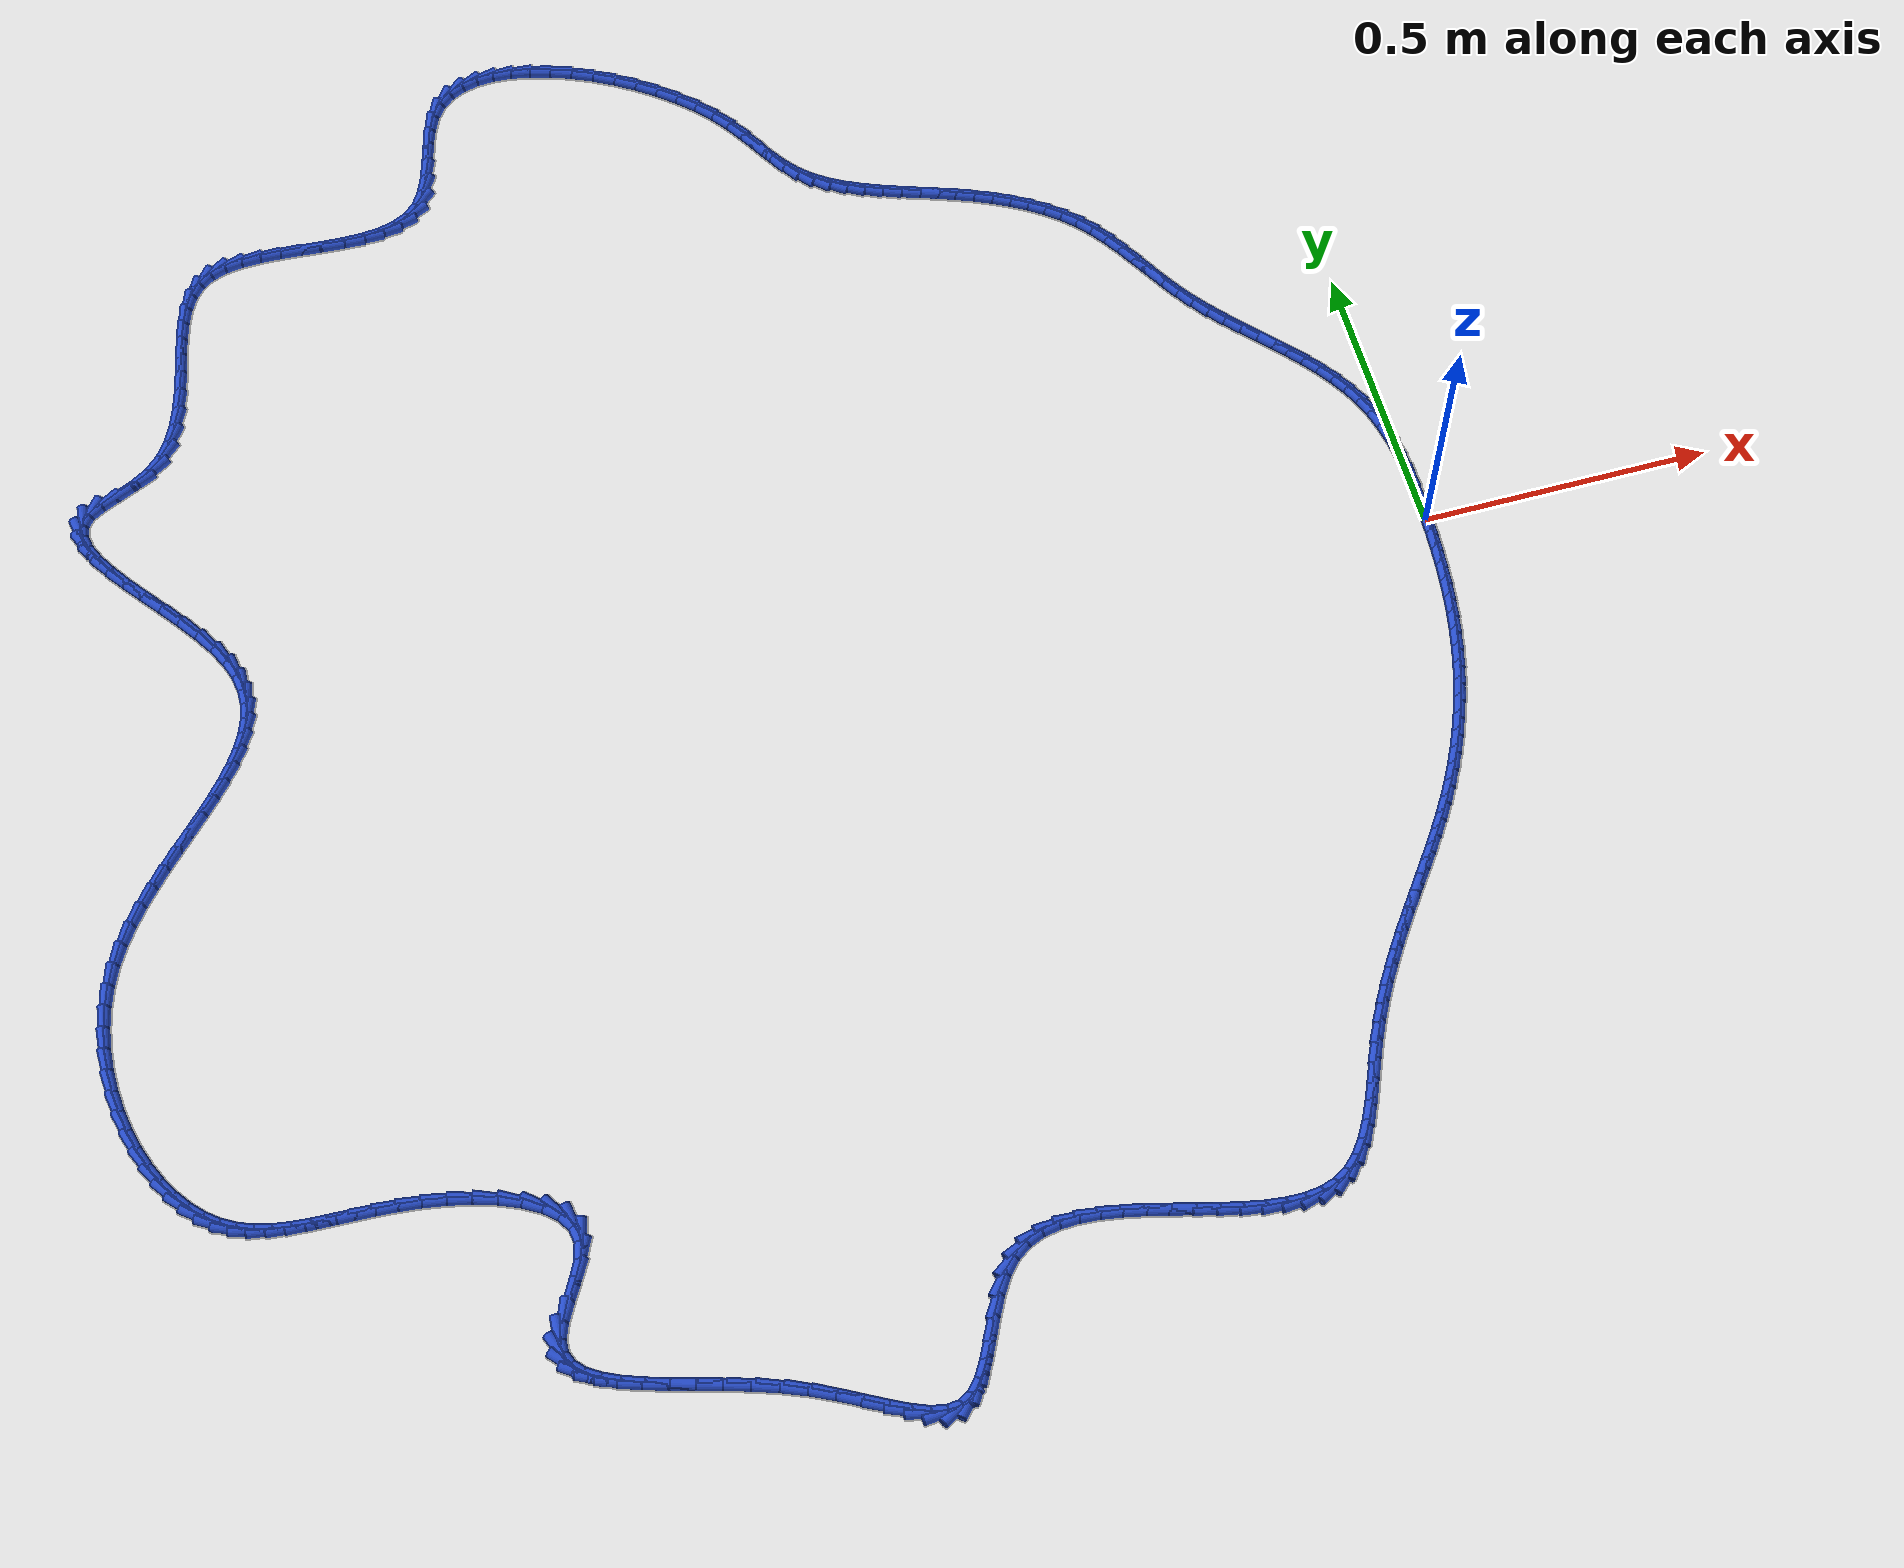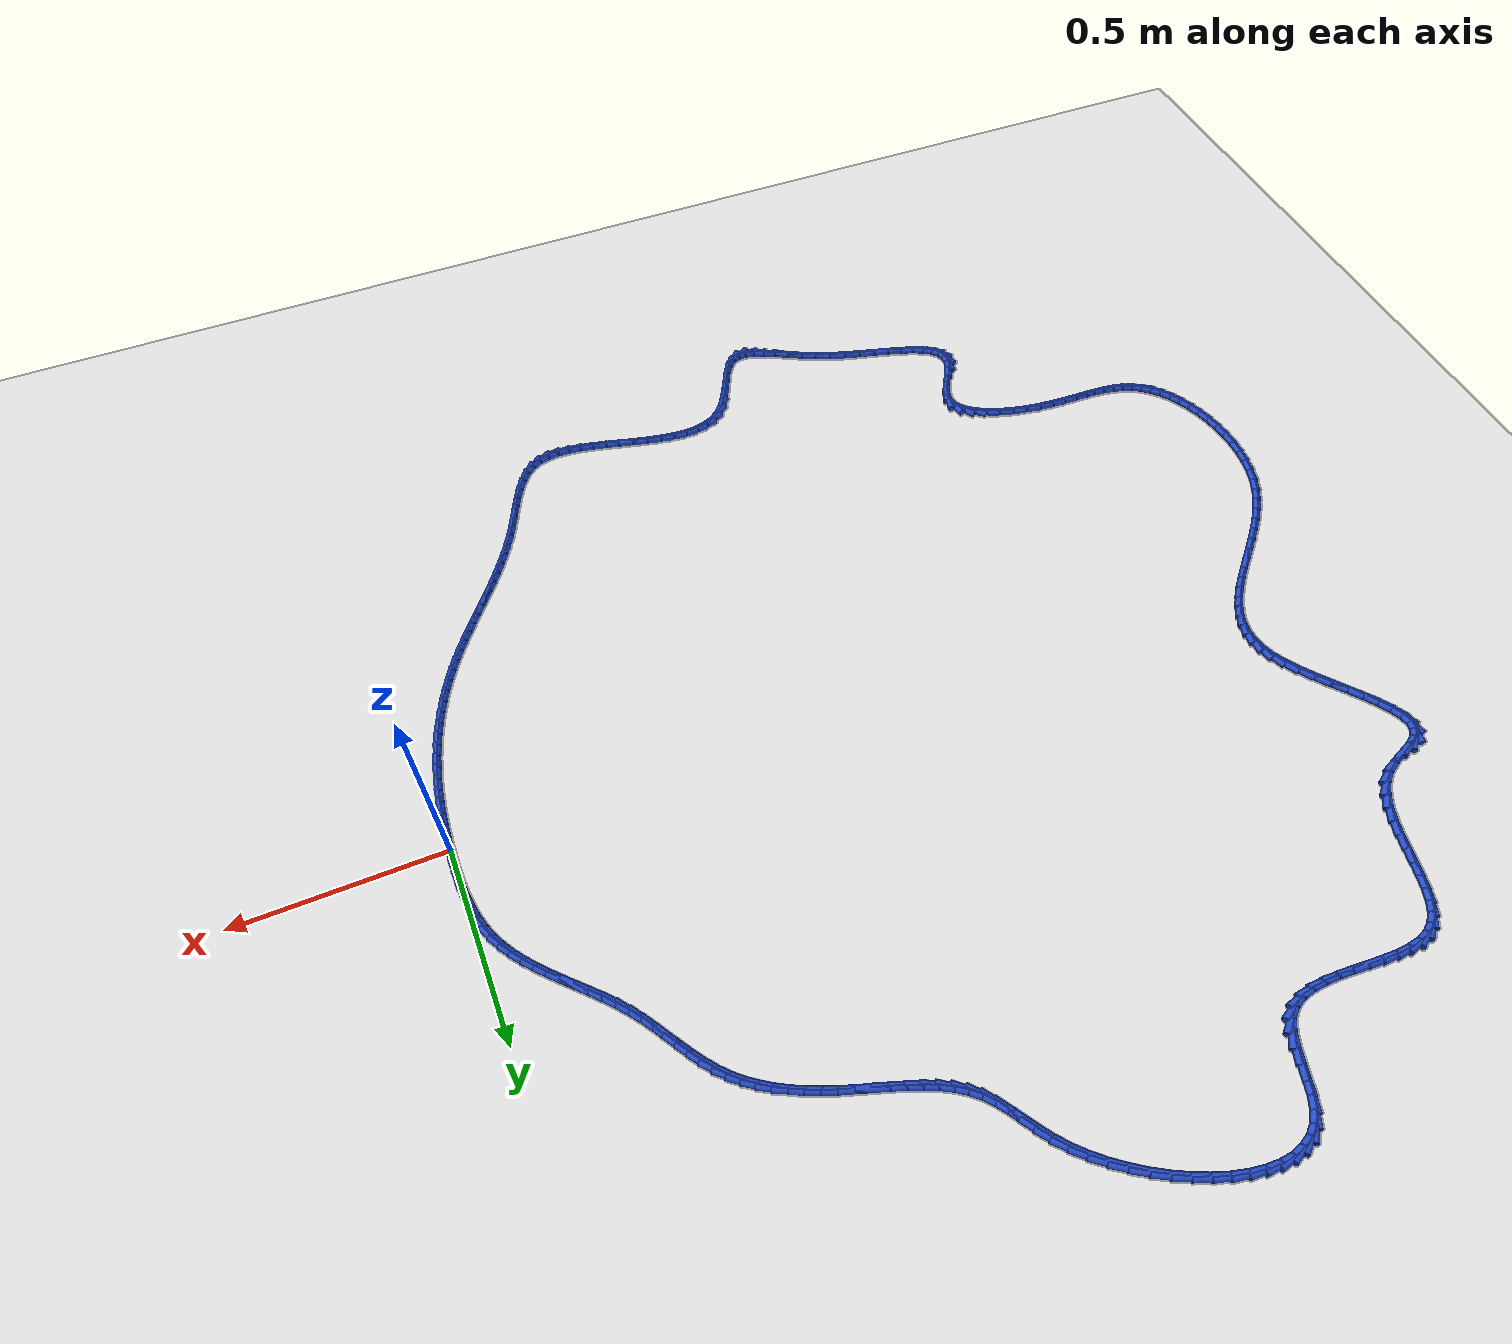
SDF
<sdf version="1.6">
 <world name="default">
  <light name="sun" type="directional">
   <pose>0 0 10 0 -0 0</pose>
   <diffuse>0.8 0.8 0.8 1</diffuse>
   <specular>0.2 0.2 0.2 1</specular>
   <attenuation>
    <range>1000</range>
    <constant>0.9</constant>
    <linear>0.01</linear>
    <quadratic>0.001</quadratic>
   </attenuation>
   <direction>-0.5 0.1 -0.9</direction>
  </light>
  <model name="ground_plane">
   <static>1</static>
   <link name="link">
    <collision name="collision">
     <geometry><plane><normal>0 0 1</normal><size>100 100</size></plane></geometry>
     <surface><friction><ode><mu>100</mu><mu2>50</mu2></ode></friction></surface>
    </collision>
    <visual name="visual">
     <cast_shadows>0</cast_shadows>
     <geometry><plane><normal>0 0 1</normal><size>100 100</size></plane></geometry>
     <material>
      <script><uri>file://media/materials/scripts/gazebo.material</uri><name>Gazebo/WhiteGlow</name></script>
     </material>
    </visual>
   </link>
  </model>
  <gravity>0 0 -9.8</gravity>
  <magnetic_field>6e-06 2.3e-05 -4.2e-05</magnetic_field>
  <atmosphere type="adiabatic"/>
  <physics name="default_physics" default="0" type="ode">
   <max_step_size>0.001</max_step_size>
   <real_time_factor>1</real_time_factor>
   <real_time_update_rate>1000</real_time_update_rate>
  </physics>
  <scene><ambient>0.4 0.4 0.4 1</ambient><background>0.7 0.7 0.7 1</background><shadows>1</shadows></scene>
  <spherical_coordinates>
   <surface_model>EARTH_WGS84</surface_model>
   <latitude_deg>0</latitude_deg>
   <longitude_deg>0</longitude_deg>
   <elevation>0</elevation>
   <heading_deg>0</heading_deg>
  </spherical_coordinates>
  <model name="line">
   <link name="link_0">
    <pose>-2.4936649967166602e-18 2.0816681711721685e-17 0.01 0 1.57 1.546620202439444</pose>
    <collision name="collision">
     <geometry><cylinder><radius>0.01</radius><length>0.08</length></cylinder></geometry>
    </collision>
    <visual name="visual">
     <material>
      <script><name>Gazebo/Blue</name><uri>file://media/materials/scripts/gazebo.material</uri></script>
     </material>
     <geometry><cylinder><radius>0.01</radius><length>0.08</length></cylinder></geometry>
    </visual>
   </link>
   <link name="link_1">
    <pose>0.0007892910329652883 0.03264118098984923 0.01 0 1.57 -1.5697717680447212</pose>
    <collision name="collision">
     <geometry><cylinder><radius>0.01</radius><length>0.08</length></cylinder></geometry>
    </collision>
    <visual name="visual">
     <material>
      <script><name>Gazebo/Blue</name><uri>file://media/materials/scripts/gazebo.material</uri></script>
     </material>
     <geometry><cylinder><radius>0.01</radius><length>0.08</length></cylinder></geometry>
    </visual>
   </link>
   <link name="link_2">
    <pose>0.0007557367479779746 0.06539115578699509 0.01 0 1.57 -1.5357777210249333</pose>
    <collision name="collision">
     <geometry><cylinder><radius>0.01</radius><length>0.08</length></cylinder></geometry>
    </collision>
    <visual name="visual">
     <material>
      <script><name>Gazebo/Blue</name><uri>file://media/materials/scripts/gazebo.material</uri></script>
     </material>
     <geometry><cylinder><radius>0.01</radius><length>0.08</length></cylinder></geometry>
    </visual>
   </link>
   <link name="link_3">
    <pose>-0.00038771334826898703 0.09803045217149915 0.01 0 1.57 -1.492329982726787</pose>
    <collision name="collision">
     <geometry><cylinder><radius>0.01</radius><length>0.08</length></cylinder></geometry>
    </collision>
    <visual name="visual">
     <material>
      <script><name>Gazebo/Blue</name><uri>file://media/materials/scripts/gazebo.material</uri></script>
     </material>
     <geometry><cylinder><radius>0.01</radius><length>0.08</length></cylinder></geometry>
    </visual>
   </link>
   <link name="link_4">
    <pose>-0.0029281097490826413 0.13033959792342292 0.01 0 1.57 -1.4385606663292798</pose>
    <collision name="collision">
     <geometry><cylinder><radius>0.01</radius><length>0.08</length></cylinder></geometry>
    </collision>
    <visual name="visual">
     <material>
      <script><name>Gazebo/Blue</name><uri>file://media/materials/scripts/gazebo.material</uri></script>
     </material>
     <geometry><cylinder><radius>0.01</radius><length>0.08</length></cylinder></geometry>
    </visual>
   </link>
   <link name="link_5">
    <pose>-0.0071525029477700315 0.1620991208228279 0.01 0 1.57 -1.3734828369184402</pose>
    <collision name="collision">
     <geometry><cylinder><radius>0.01</radius><length>0.08</length></cylinder></geometry>
    </collision>
    <visual name="visual">
     <material>
      <script><name>Gazebo/Blue</name><uri>file://media/materials/scripts/gazebo.material</uri></script>
     </material>
     <geometry><cylinder><radius>0.01</radius><length>0.08</length></cylinder></geometry>
    </visual>
   </link>
   <link name="link_6">
    <pose>-0.013347943437638201 0.19308954864977562 0.01 0 1.57 -1.296149713333827</pose>
    <collision name="collision">
     <geometry><cylinder><radius>0.01</radius><length>0.08</length></cylinder></geometry>
    </collision>
    <visual name="visual">
     <material>
      <script><name>Gazebo/Blue</name><uri>file://media/materials/scripts/gazebo.material</uri></script>
     </material>
     <geometry><cylinder><radius>0.01</radius><length>0.08</length></cylinder></geometry>
    </visual>
   </link>
   <link name="link_7">
    <pose>-0.02180148171199419 0.2230914091843275 0.01 0 1.57 -1.2059257523534648</pose>
    <collision name="collision">
     <geometry><cylinder><radius>0.01</radius><length>0.08</length></cylinder></geometry>
    </collision>
    <visual name="visual">
     <material>
      <script><name>Gazebo/Blue</name><uri>file://media/materials/scripts/gazebo.material</uri></script>
     </material>
     <geometry><cylinder><radius>0.01</radius><length>0.08</length></cylinder></geometry>
    </visual>
   </link>
   <link name="link_8">
    <pose>-0.032800005527298864 0.25188533559755705 0.01 0 1.57 -1.1087909732325651</pose>
    <collision name="collision">
     <geometry><cylinder><radius>0.01</radius><length>0.08</length></cylinder></geometry>
    </collision>
    <visual name="visual">
     <material>
      <script><name>Gazebo/Blue</name><uri>file://media/materials/scripts/gazebo.material</uri></script>
     </material>
     <geometry><cylinder><radius>0.01</radius><length>0.08</length></cylinder></geometry>
    </visual>
   </link>
   <link name="link_9">
    <pose>-0.04647673897958539 0.27935147613064515 0.01 0 1.57 -1.0229397517726437</pose>
    <collision name="collision">
     <geometry><cylinder><radius>0.01</radius><length>0.08</length></cylinder></geometry>
    </collision>
    <visual name="visual">
     <material>
      <script><name>Gazebo/Blue</name><uri>file://media/materials/scripts/gazebo.material</uri></script>
     </material>
     <geometry><cylinder><radius>0.01</radius><length>0.08</length></cylinder></geometry>
    </visual>
   </link>
   <link name="link_10">
    <pose>-0.06252572820431748 0.3056543977703248 0.01 0 1.57 -0.9524612043250442</pose>
    <collision name="collision">
     <geometry><cylinder><radius>0.01</radius><length>0.08</length></cylinder></geometry>
    </collision>
    <visual name="visual">
     <material>
      <script><name>Gazebo/Blue</name><uri>file://media/materials/scripts/gazebo.material</uri></script>
     </material>
     <geometry><cylinder><radius>0.01</radius><length>0.08</length></cylinder></geometry>
    </visual>
   </link>
   <link name="link_11">
    <pose>-0.08056306454100882 0.331009152289144 0.01 0 1.57 -0.8974322640038043</pose>
    <collision name="collision">
     <geometry><cylinder><radius>0.01</radius><length>0.08</length></cylinder></geometry>
    </collision>
    <visual name="visual">
     <material>
      <script><name>Gazebo/Blue</name><uri>file://media/materials/scripts/gazebo.material</uri></script>
     </material>
     <geometry><cylinder><radius>0.01</radius><length>0.08</length></cylinder></geometry>
    </visual>
   </link>
   <link name="link_12">
    <pose>-0.10020483932917305 0.3556307914596505 0.01 0 1.57 -0.8573566042983941</pose>
    <collision name="collision">
     <geometry><cylinder><radius>0.01</radius><length>0.08</length></cylinder></geometry>
    </collision>
    <visual name="visual">
     <material>
      <script><name>Gazebo/Blue</name><uri>file://media/materials/scripts/gazebo.material</uri></script>
     </material>
     <geometry><cylinder><radius>0.01</radius><length>0.08</length></cylinder></geometry>
    </visual>
   </link>
   <link name="link_13">
    <pose>-0.12106714390832375 0.3797343670543919 0.01 0 1.57 -0.8315557217658187</pose>
    <collision name="collision">
     <geometry><cylinder><radius>0.01</radius><length>0.08</length></cylinder></geometry>
    </collision>
    <visual name="visual">
     <material>
      <script><name>Gazebo/Blue</name><uri>file://media/materials/scripts/gazebo.material</uri></script>
     </material>
     <geometry><cylinder><radius>0.01</radius><length>0.08</length></cylinder></geometry>
    </visual>
   </link>
   <link name="link_14">
    <pose>-0.14276606961797447 0.4035349308459162 0.01 0 1.57 -0.8194195103355466</pose>
    <collision name="collision">
     <geometry><cylinder><radius>0.01</radius><length>0.08</length></cylinder></geometry>
    </collision>
    <visual name="visual">
     <material>
      <script><name>Gazebo/Blue</name><uri>file://media/materials/scripts/gazebo.material</uri></script>
     </material>
     <geometry><cylinder><radius>0.01</radius><length>0.08</length></cylinder></geometry>
    </visual>
   </link>
   <link name="link_15">
    <pose>-0.16491770779763892 0.42724753460677123 0.01 0 1.57 -0.8205388951389542</pose>
    <collision name="collision">
     <geometry><cylinder><radius>0.01</radius><length>0.08</length></cylinder></geometry>
    </collision>
    <visual name="visual">
     <material>
      <script><name>Gazebo/Blue</name><uri>file://media/materials/scripts/gazebo.material</uri></script>
     </material>
     <geometry><cylinder><radius>0.01</radius><length>0.08</length></cylinder></geometry>
    </visual>
   </link>
   <link name="link_16">
    <pose>-0.18713814978683072 0.4510872301095047 0.01 0 1.57 -0.8347536084318834</pose>
    <collision name="collision">
     <geometry><cylinder><radius>0.01</radius><length>0.08</length></cylinder></geometry>
    </collision>
    <visual name="visual">
     <material>
      <script><name>Gazebo/Blue</name><uri>file://media/materials/scripts/gazebo.material</uri></script>
     </material>
     <geometry><cylinder><radius>0.01</radius><length>0.08</length></cylinder></geometry>
    </visual>
   </link>
   <link name="link_17">
    <pose>-0.20904348692506347 0.47526906912666445 0.01 0 1.57 -0.8621365686876414</pose>
    <collision name="collision">
     <geometry><cylinder><radius>0.01</radius><length>0.08</length></cylinder></geometry>
    </collision>
    <visual name="visual">
     <material>
      <script><name>Gazebo/Blue</name><uri>file://media/materials/scripts/gazebo.material</uri></script>
     </material>
     <geometry><cylinder><radius>0.01</radius><length>0.08</length></cylinder></geometry>
    </visual>
   </link>
   <link name="link_18">
    <pose>-0.2302498105518508 0.5000081034307984 0.01 0 1.57 -0.902919579062575</pose>
    <collision name="collision">
     <geometry><cylinder><radius>0.01</radius><length>0.08</length></cylinder></geometry>
    </collision>
    <visual name="visual">
     <material>
      <script><name>Gazebo/Blue</name><uri>file://media/materials/scripts/gazebo.material</uri></script>
     </material>
     <geometry><cylinder><radius>0.01</radius><length>0.08</length></cylinder></geometry>
    </visual>
   </link>
   <link name="link_19">
    <pose>-0.25037321200670615 0.525519384794454 0.01 0 1.57 -0.9562740191444623</pose>
    <collision name="collision">
     <geometry><cylinder><radius>0.01</radius><length>0.08</length></cylinder></geometry>
    </collision>
    <visual name="visual">
     <material>
      <script><name>Gazebo/Blue</name><uri>file://media/materials/scripts/gazebo.material</uri></script>
     </material>
     <geometry><cylinder><radius>0.01</radius><length>0.08</length></cylinder></geometry>
    </visual>
   </link>
   <link name="link_20">
    <pose>-0.269058239736302 0.5519977443954881 0.01 0 1.57 -1.0041918876763616</pose>
    <collision name="collision">
     <geometry><cylinder><radius>0.01</radius><length>0.08</length></cylinder></geometry>
    </collision>
    <visual name="visual">
     <material>
      <script><name>Gazebo/Blue</name><uri>file://media/materials/scripts/gazebo.material</uri></script>
     </material>
     <geometry><cylinder><radius>0.01</radius><length>0.08</length></cylinder></geometry>
    </visual>
   </link>
   <link name="link_21">
    <pose>-0.28642684535137025 0.5792987879300152 0.01 0 1.57 -1.0316755540721156</pose>
    <collision name="collision">
     <geometry><cylinder><radius>0.01</radius><length>0.08</length></cylinder></geometry>
    </collision>
    <visual name="visual">
     <material>
      <script><name>Gazebo/Blue</name><uri>file://media/materials/scripts/gazebo.material</uri></script>
     </material>
     <geometry><cylinder><radius>0.01</radius><length>0.08</length></cylinder></geometry>
    </visual>
   </link>
   <link name="link_22">
    <pose>-0.30299680560455344 0.6069968620146992 0.01 0 1.57 -1.038269429202816</pose>
    <collision name="collision">
     <geometry><cylinder><radius>0.01</radius><length>0.08</length></cylinder></geometry>
    </collision>
    <visual name="visual">
     <material>
      <script><name>Gazebo/Blue</name><uri>file://media/materials/scripts/gazebo.material</uri></script>
     </material>
     <geometry><cylinder><radius>0.01</radius><length>0.08</length></cylinder></geometry>
    </visual>
   </link>
   <link name="link_23">
    <pose>-0.3192978589450694 0.6346578137157438 0.01 0 1.57 -1.0236949873662207</pose>
    <collision name="collision">
     <geometry><cylinder><radius>0.01</radius><length>0.08</length></cylinder></geometry>
    </collision>
    <visual name="visual">
     <material>
      <script><name>Gazebo/Blue</name><uri>file://media/materials/scripts/gazebo.material</uri></script>
     </material>
     <geometry><cylinder><radius>0.01</radius><length>0.08</length></cylinder></geometry>
    </visual>
   </link>
   <link name="link_24">
    <pose>-0.3358597438221362 0.6618474900993521 0.01 0 1.57 -0.9872947692441345</pose>
    <collision name="collision">
     <geometry><cylinder><radius>0.01</radius><length>0.08</length></cylinder></geometry>
    </collision>
    <visual name="visual">
     <material>
      <script><name>Gazebo/Blue</name><uri>file://media/materials/scripts/gazebo.material</uri></script>
     </material>
     <geometry><cylinder><radius>0.01</radius><length>0.08</length></cylinder></geometry>
    </visual>
   </link>
   <link name="link_25">
    <pose>-0.3532121986849716 0.688131738231727 0.01 0 1.57 -0.9282127430467669</pose>
    <collision name="collision">
     <geometry><cylinder><radius>0.01</radius><length>0.08</length></cylinder></geometry>
    </collision>
    <visual name="visual">
     <material>
      <script><name>Gazebo/Blue</name><uri>file://media/materials/scripts/gazebo.material</uri></script>
     </material>
     <geometry><cylinder><radius>0.01</radius><length>0.08</length></cylinder></geometry>
    </visual>
   </link>
   <link name="link_26">
    <pose>-0.37188496198279364 0.7130764051790719 0.01 0 1.57 -0.8460910870579929</pose>
    <collision name="collision">
     <geometry><cylinder><radius>0.01</radius><length>0.08</length></cylinder></geometry>
    </collision>
    <visual name="visual">
     <material>
      <script><name>Gazebo/Blue</name><uri>file://media/materials/scripts/gazebo.material</uri></script>
     </material>
     <geometry><cylinder><radius>0.01</radius><length>0.08</length></cylinder></geometry>
    </visual>
   </link>
   <link name="link_27">
    <pose>-0.3924038790254911 0.7362504359200281 0.01 0 1.57 -0.7524700737849487</pose>
    <collision name="collision">
     <geometry><cylinder><radius>0.01</radius><length>0.08</length></cylinder></geometry>
    </collision>
    <visual name="visual">
     <material>
      <script><name>Gazebo/Blue</name><uri>file://media/materials/scripts/gazebo.material</uri></script>
     </material>
     <geometry><cylinder><radius>0.01</radius><length>0.08</length></cylinder></geometry>
    </visual>
   </link>
   <link name="link_28">
    <pose>-0.4150299996812504 0.7574334827887017 0.01 0 1.57 -0.6662824770688995</pose>
    <collision name="collision">
     <geometry><cylinder><radius>0.01</radius><length>0.08</length></cylinder></geometry>
    </collision>
    <visual name="visual">
     <material>
      <script><name>Gazebo/Blue</name><uri>file://media/materials/scripts/gazebo.material</uri></script>
     </material>
     <geometry><cylinder><radius>0.01</radius><length>0.08</length></cylinder></geometry>
    </visual>
   </link>
   <link name="link_29">
    <pose>-0.4395949139577021 0.7767469349365453 0.01 0 1.57 -0.589732814284087</pose>
    <collision name="collision">
     <geometry><cylinder><radius>0.01</radius><length>0.08</length></cylinder></geometry>
    </collision>
    <visual name="visual">
     <material>
      <script><name>Gazebo/Blue</name><uri>file://media/materials/scripts/gazebo.material</uri></script>
     </material>
     <geometry><cylinder><radius>0.01</radius><length>0.08</length></cylinder></geometry>
    </visual>
   </link>
   <link name="link_30">
    <pose>-0.46589095214302206 0.7943434219004566 0.01 0 1.57 -0.5228047211377633</pose>
    <collision name="collision">
     <geometry><cylinder><radius>0.01</radius><length>0.08</length></cylinder></geometry>
    </collision>
    <visual name="visual">
     <material>
      <script><name>Gazebo/Blue</name><uri>file://media/materials/scripts/gazebo.material</uri></script>
     </material>
     <geometry><cylinder><radius>0.01</radius><length>0.08</length></cylinder></geometry>
    </visual>
   </link>
   <link name="link_31">
    <pose>-0.49371044452538637 0.8103755732173324 0.01 0 1.57 -0.46509653237290854</pose>
    <collision name="collision">
     <geometry><cylinder><radius>0.01</radius><length>0.08</length></cylinder></geometry>
    </collision>
    <visual name="visual">
     <material>
      <script><name>Gazebo/Blue</name><uri>file://media/materials/scripts/gazebo.material</uri></script>
     </material>
     <geometry><cylinder><radius>0.01</radius><length>0.08</length></cylinder></geometry>
    </visual>
   </link>
   <link name="link_32">
    <pose>-0.5228457213929708 0.8249960184240699 0.01 0 1.57 -0.4160094403022977</pose>
    <collision name="collision">
     <geometry><cylinder><radius>0.01</radius><length>0.08</length></cylinder></geometry>
    </collision>
    <visual name="visual">
     <material>
      <script><name>Gazebo/Blue</name><uri>file://media/materials/scripts/gazebo.material</uri></script>
     </material>
     <geometry><cylinder><radius>0.01</radius><length>0.08</length></cylinder></geometry>
    </visual>
   </link>
   <link name="link_33">
    <pose>-0.5530891130339515 0.838357387057566 0.01 0 1.57 -0.3748960228453026</pose>
    <collision name="collision">
     <geometry><cylinder><radius>0.01</radius><length>0.08</length></cylinder></geometry>
    </collision>
    <visual name="visual">
     <material>
      <script><name>Gazebo/Blue</name><uri>file://media/materials/scripts/gazebo.material</uri></script>
     </material>
     <geometry><cylinder><radius>0.01</radius><length>0.08</length></cylinder></geometry>
    </visual>
   </link>
   <link name="link_34">
    <pose>-0.584232723520706 0.850612600007954 0.01 0 1.57 -0.3438564441189873</pose>
    <collision name="collision">
     <geometry><cylinder><radius>0.01</radius><length>0.08</length></cylinder></geometry>
    </collision>
    <visual name="visual">
     <material>
      <script><name>Gazebo/Blue</name><uri>file://media/materials/scripts/gazebo.material</uri></script>
     </material>
     <geometry><cylinder><radius>0.01</radius><length>0.08</length></cylinder></geometry>
    </visual>
   </link>
   <link name="link_35">
    <pose>-0.616009185774971 0.8619911736653764 0.01 0 1.57 -0.32855671468374964</pose>
    <collision name="collision">
     <geometry><cylinder><radius>0.01</radius><length>0.08</length></cylinder></geometry>
    </collision>
    <visual name="visual">
     <material>
      <script><name>Gazebo/Blue</name><uri>file://media/materials/scripts/gazebo.material</uri></script>
     </material>
     <geometry><cylinder><radius>0.01</radius><length>0.08</length></cylinder></geometry>
    </visual>
   </link>
   <link name="link_36">
    <pose>-0.6480122879130841 0.8729014487268673 0.01 0 1.57 -0.3294994629025114</pose>
    <collision name="collision">
     <geometry><cylinder><radius>0.01</radius><length>0.08</length></cylinder></geometry>
    </collision>
    <visual name="visual">
     <material>
      <script><name>Gazebo/Blue</name><uri>file://media/materials/scripts/gazebo.material</uri></script>
     </material>
     <geometry><cylinder><radius>0.01</radius><length>0.08</length></cylinder></geometry>
    </visual>
   </link>
   <link name="link_37">
    <pose>-0.6798160386413575 0.8837772406580571 0.01 0 1.57 -0.34699999095266437</pose>
    <collision name="collision">
     <geometry><cylinder><radius>0.01</radius><length>0.08</length></cylinder></geometry>
    </collision>
    <visual name="visual">
     <material>
      <script><name>Gazebo/Blue</name><uri>file://media/materials/scripts/gazebo.material</uri></script>
     </material>
     <geometry><cylinder><radius>0.01</radius><length>0.08</length></cylinder></geometry>
    </visual>
   </link>
   <link name="link_38">
    <pose>-0.7109944466661047 0.8950523649245756 0.01 0 1.57 -0.3821489786543776</pose>
    <collision name="collision">
     <geometry><cylinder><radius>0.01</radius><length>0.08</length></cylinder></geometry>
    </collision>
    <visual name="visual">
     <material>
      <script><name>Gazebo/Blue</name><uri>file://media/materials/scripts/gazebo.material</uri></script>
     </material>
     <geometry><cylinder><radius>0.01</radius><length>0.08</length></cylinder></geometry>
    </visual>
   </link>
   <link name="link_39">
    <pose>-0.741121520693638 0.9071606369920532 0.01 0 1.57 -0.43678056641381036</pose>
    <collision name="collision">
     <geometry><cylinder><radius>0.01</radius><length>0.08</length></cylinder></geometry>
    </collision>
    <visual name="visual">
     <material>
      <script><name>Gazebo/Blue</name><uri>file://media/materials/scripts/gazebo.material</uri></script>
     </material>
     <geometry><cylinder><radius>0.01</radius><length>0.08</length></cylinder></geometry>
    </visual>
   </link>
   <link name="link_40">
    <pose>-0.7697712694302705 0.9205358723261201 0.01 0 1.57 -0.5132736186744208</pose>
    <collision name="collision">
     <geometry><cylinder><radius>0.01</radius><length>0.08</length></cylinder></geometry>
    </collision>
    <visual name="visual">
     <material>
      <script><name>Gazebo/Blue</name><uri>file://media/materials/scripts/gazebo.material</uri></script>
     </material>
     <geometry><cylinder><radius>0.01</radius><length>0.08</length></cylinder></geometry>
    </visual>
   </link>
   <link name="link_41">
    <pose>-0.7965177015823152 0.9356118863924064 0.01 0 1.57 -0.6139790102619098</pose>
    <collision name="collision">
     <geometry><cylinder><radius>0.01</radius><length>0.08</length></cylinder></geometry>
    </collision>
    <visual name="visual">
     <material>
      <script><name>Gazebo/Blue</name><uri>file://media/materials/scripts/gazebo.material</uri></script>
     </material>
     <geometry><cylinder><radius>0.01</radius><length>0.08</length></cylinder></geometry>
    </visual>
   </link>
   <link name="link_42">
    <pose>-0.8209348258560843 0.9528224946565423 0.01 0 1.57 -0.7399957735964606</pose>
    <collision name="collision">
     <geometry><cylinder><radius>0.01</radius><length>0.08</length></cylinder></geometry>
    </collision>
    <visual name="visual">
     <material>
      <script><name>Gazebo/Blue</name><uri>file://media/materials/scripts/gazebo.material</uri></script>
     </material>
     <geometry><cylinder><radius>0.01</radius><length>0.08</length></cylinder></geometry>
    </visual>
   </link>
   <link name="link_43">
    <pose>-0.8425966509811885 0.9726015125693708 0.01 0 1.57 -0.8779175972005473</pose>
    <collision name="collision">
     <geometry><cylinder><radius>0.01</radius><length>0.08</length></cylinder></geometry>
    </collision>
    <visual name="visual">
     <material>
      <script><name>Gazebo/Blue</name><uri>file://media/materials/scripts/gazebo.material</uri></script>
     </material>
     <geometry><cylinder><radius>0.01</radius><length>0.08</length></cylinder></geometry>
    </visual>
   </link>
   <link name="link_44">
    <pose>-0.8613602162522479 0.9952031172015621 0.01 0 1.57 -0.9774447620086186</pose>
    <collision name="collision">
     <geometry><cylinder><radius>0.01</radius><length>0.08</length></cylinder></geometry>
    </collision>
    <visual name="visual">
     <material>
      <script><name>Gazebo/Blue</name><uri>file://media/materials/scripts/gazebo.material</uri></script>
     </material>
     <geometry><cylinder><radius>0.01</radius><length>0.08</length></cylinder></geometry>
    </visual>
   </link>
   <link name="link_45">
    <pose>-0.878199941521659 1.020172288603212 0.01 0 1.57 -1.02647708353751</pose>
    <collision name="collision">
     <geometry><cylinder><radius>0.01</radius><length>0.08</length></cylinder></geometry>
    </collision>
    <visual name="visual">
     <material>
      <script><name>Gazebo/Blue</name><uri>file://media/materials/scripts/gazebo.material</uri></script>
     </material>
     <geometry><cylinder><radius>0.01</radius><length>0.08</length></cylinder></geometry>
    </visual>
   </link>
   <link name="link_46">
    <pose>-0.894365954219529 1.0468790163153185 0.01 0 1.57 -1.0289541174394816</pose>
    <collision name="collision">
     <geometry><cylinder><radius>0.01</radius><length>0.08</length></cylinder></geometry>
    </collision>
    <visual name="visual">
     <material>
      <script><name>Gazebo/Blue</name><uri>file://media/materials/scripts/gazebo.material</uri></script>
     </material>
     <geometry><cylinder><radius>0.01</radius><length>0.08</length></cylinder></geometry>
    </visual>
   </link>
   <link name="link_47">
    <pose>-0.9111083817759654 1.0746932898788784 0.01 0 1.57 -0.9899789465877593</pose>
    <collision name="collision">
     <geometry><cylinder><radius>0.01</radius><length>0.08</length></cylinder></geometry>
    </collision>
    <visual name="visual">
     <material>
      <script><name>Gazebo/Blue</name><uri>file://media/materials/scripts/gazebo.material</uri></script>
     </material>
     <geometry><cylinder><radius>0.01</radius><length>0.08</length></cylinder></geometry>
    </visual>
   </link>
   <link name="link_48">
    <pose>-0.9296773516210755 1.1029850988348895 0.01 0 1.57 -0.9154479659616122</pose>
    <collision name="collision">
     <geometry><cylinder><radius>0.01</radius><length>0.08</length></cylinder></geometry>
    </collision>
    <visual name="visual">
     <material>
      <script><name>Gazebo/Blue</name><uri>file://media/materials/scripts/gazebo.material</uri></script>
     </material>
     <geometry><cylinder><radius>0.01</radius><length>0.08</length></cylinder></geometry>
    </visual>
   </link>
   <link name="link_49">
    <pose>-0.95130917641502 1.1311266874326276 0.01 0 1.57 -0.82780920466849</pose>
    <collision name="collision">
     <geometry><cylinder><radius>0.01</radius><length>0.08</length></cylinder></geometry>
    </collision>
    <visual name="visual">
     <material>
      <script><name>Gazebo/Blue</name><uri>file://media/materials/scripts/gazebo.material</uri></script>
     </material>
     <geometry><cylinder><radius>0.01</radius><length>0.08</length></cylinder></geometry>
    </visual>
   </link>
   <link name="link_50">
    <pose>-0.9765485848931763 1.1586031733174933 0.01 0 1.57 -0.750183507608094</pose>
    <collision name="collision">
     <geometry><cylinder><radius>0.01</radius><length>0.08</length></cylinder></geometry>
    </collision>
    <visual name="visual">
     <material>
      <script><name>Gazebo/Blue</name><uri>file://media/materials/scripts/gazebo.material</uri></script>
     </material>
     <geometry><cylinder><radius>0.01</radius><length>0.08</length></cylinder></geometry>
    </visual>
   </link>
   <link name="link_51">
    <pose>-1.0049406259810947 1.1850628318531753 0.01 0 1.57 -0.6805051637333096</pose>
    <collision name="collision">
     <geometry><cylinder><radius>0.01</radius><length>0.08</length></cylinder></geometry>
    </collision>
    <visual name="visual">
     <material>
      <script><name>Gazebo/Blue</name><uri>file://media/materials/scripts/gazebo.material</uri></script>
     </material>
     <geometry><cylinder><radius>0.01</radius><length>0.08</length></cylinder></geometry>
    </visual>
   </link>
   <link name="link_52">
    <pose>-1.0359522803015115 1.2101666799292319 0.01 0 1.57 -0.6155815954547789</pose>
    <collision name="collision">
     <geometry><cylinder><radius>0.01</radius><length>0.08</length></cylinder></geometry>
    </collision>
    <visual name="visual">
     <material>
      <script><name>Gazebo/Blue</name><uri>file://media/materials/scripts/gazebo.material</uri></script>
     </material>
     <geometry><cylinder><radius>0.01</radius><length>0.08</length></cylinder></geometry>
    </visual>
   </link>
   <link name="link_53">
    <pose>-1.0690505284771623 1.2335757344352194 0.01 0 1.57 -0.5527234555478191</pose>
    <collision name="collision">
     <geometry><cylinder><radius>0.01</radius><length>0.08</length></cylinder></geometry>
    </collision>
    <visual name="visual">
     <material>
      <script><name>Gazebo/Blue</name><uri>file://media/materials/scripts/gazebo.material</uri></script>
     </material>
     <geometry><cylinder><radius>0.01</radius><length>0.08</length></cylinder></geometry>
    </visual>
   </link>
   <link name="link_54">
    <pose>-1.1037023511307842 1.2549510122606977 0.01 0 1.57 -0.4894606756892485</pose>
    <collision name="collision">
     <geometry><cylinder><radius>0.01</radius><length>0.08</length></cylinder></geometry>
    </collision>
    <visual name="visual">
     <material>
      <script><name>Gazebo/Blue</name><uri>file://media/materials/scripts/gazebo.material</uri></script>
     </material>
     <geometry><cylinder><radius>0.01</radius><length>0.08</length></cylinder></geometry>
    </visual>
   </link>
   <link name="link_55">
    <pose>-1.1393747288851126 1.2739535302952232 0.01 0 1.57 -0.423286525286652</pose>
    <collision name="collision">
     <geometry><cylinder><radius>0.01</radius><length>0.08</length></cylinder></geometry>
    </collision>
    <visual name="visual">
     <material>
      <script><name>Gazebo/Blue</name><uri>file://media/materials/scripts/gazebo.material</uri></script>
     </material>
     <geometry><cylinder><radius>0.01</radius><length>0.08</length></cylinder></geometry>
    </visual>
   </link>
   <link name="link_56">
    <pose>-1.175534642362884 1.2902443054283539 0.01 0 1.57 -0.3513982105993717</pose>
    <collision name="collision">
     <geometry><cylinder><radius>0.01</radius><length>0.08</length></cylinder></geometry>
    </collision>
    <visual name="visual">
     <material>
      <script><name>Gazebo/Blue</name><uri>file://media/materials/scripts/gazebo.material</uri></script>
     </material>
     <geometry><cylinder><radius>0.01</radius><length>0.08</length></cylinder></geometry>
    </visual>
   </link>
   <link name="link_57">
    <pose>-1.2116490721868352 1.3034843545496482 0.01 0 1.57 -0.2704046601474207</pose>
    <collision name="collision">
     <geometry><cylinder><radius>0.01</radius><length>0.08</length></cylinder></geometry>
    </collision>
    <visual name="visual">
     <material>
      <script><name>Gazebo/Blue</name><uri>file://media/materials/scripts/gazebo.material</uri></script>
     </material>
     <geometry><cylinder><radius>0.01</radius><length>0.08</length></cylinder></geometry>
    </visual>
   </link>
   <link name="link_58">
    <pose>-1.2471849989797017 1.3133346945486633 0.01 0 1.57 -0.17598900648020238</pose>
    <collision name="collision">
     <geometry><cylinder><radius>0.01</radius><length>0.08</length></cylinder></geometry>
    </collision>
    <visual name="visual">
     <material>
      <script><name>Gazebo/Blue</name><uri>file://media/materials/scripts/gazebo.material</uri></script>
     </material>
     <geometry><cylinder><radius>0.01</radius><length>0.08</length></cylinder></geometry>
    </visual>
   </link>
   <link name="link_59">
    <pose>-1.2816094033642194 1.319456342314957 0.01 0 1.57 -0.06257776748838324</pose>
    <collision name="collision">
     <geometry><cylinder><radius>0.01</radius><length>0.08</length></cylinder></geometry>
    </collision>
    <visual name="visual">
     <material>
      <script><name>Gazebo/Blue</name><uri>file://media/materials/scripts/gazebo.material</uri></script>
     </material>
     <geometry><cylinder><radius>0.01</radius><length>0.08</length></cylinder></geometry>
    </visual>
   </link>
   <link name="link_60">
    <pose>-1.3143892659631247 1.3215103147380876 0.01 0 1.57 0.07672845350002035</pose>
    <collision name="collision">
     <geometry><cylinder><radius>0.01</radius><length>0.08</length></cylinder></geometry>
    </collision>
    <visual name="visual">
     <material>
      <script><name>Gazebo/Blue</name><uri>file://media/materials/scripts/gazebo.material</uri></script>
     </material>
     <geometry><cylinder><radius>0.01</radius><length>0.08</length></cylinder></geometry>
    </visual>
   </link>
   <link name="link_61">
    <pose>-1.3449915673991546 1.3191576287076126 0.01 0 1.57 0.24920556745682332</pose>
    <collision name="collision">
     <geometry><cylinder><radius>0.01</radius><length>0.08</length></cylinder></geometry>
    </collision>
    <visual name="visual">
     <material>
      <script><name>Gazebo/Blue</name><uri>file://media/materials/scripts/gazebo.material</uri></script>
     </material>
     <geometry><cylinder><radius>0.01</radius><length>0.08</length></cylinder></geometry>
    </visual>
   </link>
   <link name="link_62">
    <pose>-1.3728832882950446 1.3120593011130899 0.01 0 1.57 0.459057203063662</pose>
    <collision name="collision">
     <geometry><cylinder><radius>0.01</radius><length>0.08</length></cylinder></geometry>
    </collision>
    <visual name="visual">
     <material>
      <script><name>Gazebo/Blue</name><uri>file://media/materials/scripts/gazebo.material</uri></script>
     </material>
     <geometry><cylinder><radius>0.01</radius><length>0.08</length></cylinder></geometry>
    </visual>
   </link>
   <link name="link_63">
    <pose>-1.397531409273531 1.299876348844077 0.01 0 1.57 0.7007488997844443</pose>
    <collision name="collision">
     <geometry><cylinder><radius>0.01</radius><length>0.08</length></cylinder></geometry>
    </collision>
    <visual name="visual">
     <material>
      <script><name>Gazebo/Blue</name><uri>file://media/materials/scripts/gazebo.material</uri></script>
     </material>
     <geometry><cylinder><radius>0.01</radius><length>0.08</length></cylinder></geometry>
    </visual>
   </link>
   <link name="link_64">
    <pose>-1.4184029109573502 1.2822697887901326 0.01 0 1.57 0.9533107730913899</pose>
    <collision name="collision">
     <geometry><cylinder><radius>0.01</radius><length>0.08</length></cylinder></geometry>
    </collision>
    <visual name="visual">
     <material>
      <script><name>Gazebo/Blue</name><uri>file://media/materials/scripts/gazebo.material</uri></script>
     </material>
     <geometry><cylinder><radius>0.01</radius><length>0.08</length></cylinder></geometry>
    </visual>
   </link>
   <link name="link_65">
    <pose>-1.4349832308209747 1.2589211661364625 0.01 0 1.57 1.1543083031571306</pose>
    <collision name="collision">
     <geometry><cylinder><radius>0.01</radius><length>0.08</length></cylinder></geometry>
    </collision>
    <visual name="visual">
     <material>
      <script><name>Gazebo/Blue</name><uri>file://media/materials/scripts/gazebo.material</uri></script>
     </material>
     <geometry><cylinder><radius>0.01</radius><length>0.08</length></cylinder></geometry>
    </visual>
   </link>
   <link name="link_66">
    <pose>-1.4475855803237752 1.230432702537639 0.01 0 1.57 1.2633749799399936</pose>
    <collision name="collision">
     <geometry><cylinder><radius>0.01</radius><length>0.08</length></cylinder></geometry>
    </collision>
    <visual name="visual">
     <material>
      <script><name>Gazebo/Blue</name><uri>file://media/materials/scripts/gazebo.material</uri></script>
     </material>
     <geometry><cylinder><radius>0.01</radius><length>0.08</length></cylinder></geometry>
    </visual>
   </link>
   <link name="link_67">
    <pose>-1.4576670085853611 1.198678832157652 0.01 0 1.57 1.3020900851127613</pose>
    <collision name="collision">
     <geometry><cylinder><radius>0.01</radius><length>0.08</length></cylinder></geometry>
    </collision>
    <visual name="visual">
     <material>
      <script><name>Gazebo/Blue</name><uri>file://media/materials/scripts/gazebo.material</uri></script>
     </material>
     <geometry><cylinder><radius>0.01</radius><length>0.08</length></cylinder></geometry>
    </visual>
   </link>
   <link name="link_68">
    <pose>-1.4667683141438332 1.1656271379188876 0.01 0 1.57 1.2808304147023837</pose>
    <collision name="collision">
     <geometry><cylinder><radius>0.01</radius><length>0.08</length></cylinder></geometry>
    </collision>
    <visual name="visual">
     <material>
      <script><name>Gazebo/Blue</name><uri>file://media/materials/scripts/gazebo.material</uri></script>
     </material>
     <geometry><cylinder><radius>0.01</radius><length>0.08</length></cylinder></geometry>
    </visual>
   </link>
   <link name="link_69">
    <pose>-1.4764302955372917 1.1332452027437339 0.01 0 1.57 1.1941907021680145</pose>
    <collision name="collision">
     <geometry><cylinder><radius>0.01</radius><length>0.08</length></cylinder></geometry>
    </collision>
    <visual name="visual">
     <material>
      <script><name>Gazebo/Blue</name><uri>file://media/materials/scripts/gazebo.material</uri></script>
     </material>
     <geometry><cylinder><radius>0.01</radius><length>0.08</length></cylinder></geometry>
    </visual>
   </link>
   <link name="link_70">
    <pose>-1.4881937513038366 1.103500609554577 0.01 0 1.57 1.021014138136253</pose>
    <collision name="collision">
     <geometry><cylinder><radius>0.01</radius><length>0.08</length></cylinder></geometry>
    </collision>
    <visual name="visual">
     <material>
      <script><name>Gazebo/Blue</name><uri>file://media/materials/scripts/gazebo.material</uri></script>
     </material>
     <geometry><cylinder><radius>0.01</radius><length>0.08</length></cylinder></geometry>
    </visual>
   </link>
   <link name="link_71">
    <pose>-1.5035994799815682 1.0783609412738042 0.01 0 1.57 0.7430011290169706</pose>
    <collision name="collision">
     <geometry><cylinder><radius>0.01</radius><length>0.08</length></cylinder></geometry>
    </collision>
    <visual name="visual">
     <material>
      <script><name>Gazebo/Blue</name><uri>file://media/materials/scripts/gazebo.material</uri></script>
     </material>
     <geometry><cylinder><radius>0.01</radius><length>0.08</length></cylinder></geometry>
    </visual>
   </link>
   <link name="link_72">
    <pose>-1.5240296808286748 1.0595935965653562 0.01 0 1.57 0.4569677788438715</pose>
    <collision name="collision">
     <geometry><cylinder><radius>0.01</radius><length>0.08</length></cylinder></geometry>
    </collision>
    <visual name="visual">
     <material>
      <script><name>Gazebo/Blue</name><uri>file://media/materials/scripts/gazebo.material</uri></script>
     </material>
     <geometry><cylinder><radius>0.01</radius><length>0.08</length></cylinder></geometry>
    </visual>
   </link>
   <link name="link_73">
    <pose>-1.5494026702221477 1.0471182588375545 0.01 0 1.57 0.24180379570897376</pose>
    <collision name="collision">
     <geometry><cylinder><radius>0.01</radius><length>0.08</length></cylinder></geometry>
    </collision>
    <visual name="visual">
     <material>
      <script><name>Gazebo/Blue</name><uri>file://media/materials/scripts/gazebo.material</uri></script>
     </material>
     <geometry><cylinder><radius>0.01</radius><length>0.08</length></cylinder></geometry>
    </visual>
   </link>
   <link name="link_74">
    <pose>-1.578846107219926 1.0398566425975548 0.01 0 1.57 0.09580015212663569</pose>
    <collision name="collision">
     <geometry><cylinder><radius>0.01</radius><length>0.08</length></cylinder></geometry>
    </collision>
    <visual name="visual">
     <material>
      <script><name>Gazebo/Blue</name><uri>file://media/materials/scripts/gazebo.material</uri></script>
     </material>
     <geometry><cylinder><radius>0.01</radius><length>0.08</length></cylinder></geometry>
    </visual>
   </link>
   <link name="link_75">
    <pose>-1.6114799307343088 1.036720717972648 0.01 0 1.57 0.0028119907480594966</pose>
    <collision name="collision">
     <geometry><cylinder><radius>0.01</radius><length>0.08</length></cylinder></geometry>
    </collision>
    <visual name="visual">
     <material>
      <script><name>Gazebo/Blue</name><uri>file://media/materials/scripts/gazebo.material</uri></script>
     </material>
     <geometry><cylinder><radius>0.01</radius><length>0.08</length></cylinder></geometry>
    </visual>
   </link>
   <link name="link_76">
    <pose>-1.6464240796775942 1.0366224550901229 0.01 0 1.57 -0.050853679966673365</pose>
    <collision name="collision">
     <geometry><cylinder><radius>0.01</radius><length>0.08</length></cylinder></geometry>
    </collision>
    <visual name="visual">
     <material>
      <script><name>Gazebo/Blue</name><uri>file://media/materials/scripts/gazebo.material</uri></script>
     </material>
     <geometry><cylinder><radius>0.01</radius><length>0.08</length></cylinder></geometry>
    </visual>
   </link>
   <link name="link_77">
    <pose>-1.682798492962081 1.0384738240772693 0.01 0 1.57 -0.07334144981078479</pose>
    <collision name="collision">
     <geometry><cylinder><radius>0.01</radius><length>0.08</length></cylinder></geometry>
    </collision>
    <visual name="visual">
     <material>
      <script><name>Gazebo/Blue</name><uri>file://media/materials/scripts/gazebo.material</uri></script>
     </material>
     <geometry><cylinder><radius>0.01</radius><length>0.08</length></cylinder></geometry>
    </visual>
   </link>
   <link name="link_78">
    <pose>-1.7197231095000678 1.041186795061376 0.01 0 1.57 -0.06784378479950667</pose>
    <collision name="collision">
     <geometry><cylinder><radius>0.01</radius><length>0.08</length></cylinder></geometry>
    </collision>
    <visual name="visual">
     <material>
      <script><name>Gazebo/Blue</name><uri>file://media/materials/scripts/gazebo.material</uri></script>
     </material>
     <geometry><cylinder><radius>0.01</radius><length>0.08</length></cylinder></geometry>
    </visual>
   </link>
   <link name="link_79">
    <pose>-1.756317868203853 1.0436733381697332 0.01 0 1.57 -0.03311183490366652</pose>
    <collision name="collision">
     <geometry><cylinder><radius>0.01</radius><length>0.08</length></cylinder></geometry>
    </collision>
    <visual name="visual">
     <material>
      <script><name>Gazebo/Blue</name><uri>file://media/materials/scripts/gazebo.material</uri></script>
     </material>
     <geometry><cylinder><radius>0.01</radius><length>0.08</length></cylinder></geometry>
    </visual>
   </link>
   <link name="link_80">
    <pose>-1.791702707985735 1.0448454235296298 0.01 0 1.57 0.03693791257811529</pose>
    <collision name="collision">
     <geometry><cylinder><radius>0.01</radius><length>0.08</length></cylinder></geometry>
    </collision>
    <visual name="visual">
     <material>
      <script><name>Gazebo/Blue</name><uri>file://media/materials/scripts/gazebo.material</uri></script>
     </material>
     <geometry><cylinder><radius>0.01</radius><length>0.08</length></cylinder></geometry>
    </visual>
   </link>
   <link name="link_81">
    <pose>-1.8249975677580126 1.0436150212683557 0.01 0 1.57 0.15443873204071865</pose>
    <collision name="collision">
     <geometry><cylinder><radius>0.01</radius><length>0.08</length></cylinder></geometry>
    </collision>
    <visual name="visual">
     <material>
      <script><name>Gazebo/Blue</name><uri>file://media/materials/scripts/gazebo.material</uri></script>
     </material>
     <geometry><cylinder><radius>0.01</radius><length>0.08</length></cylinder></geometry>
    </visual>
   </link>
   <link name="link_82">
    <pose>-1.855322386432983 1.0388941015131996 0.01 0 1.57 0.3377954673193905</pose>
    <collision name="collision">
     <geometry><cylinder><radius>0.01</radius><length>0.08</length></cylinder></geometry>
    </collision>
    <visual name="visual">
     <material>
      <script><name>Gazebo/Blue</name><uri>file://media/materials/scripts/gazebo.material</uri></script>
     </material>
     <geometry><cylinder><radius>0.01</radius><length>0.08</length></cylinder></geometry>
    </visual>
   </link>
   <link name="link_83">
    <pose>-1.8817971029229468 1.0295946343914515 0.01 0 1.57 0.5992361138544208</pose>
    <collision name="collision">
     <geometry><cylinder><radius>0.01</radius><length>0.08</length></cylinder></geometry>
    </collision>
    <visual name="visual">
     <material>
      <script><name>Gazebo/Blue</name><uri>file://media/materials/scripts/gazebo.material</uri></script>
     </material>
     <geometry><cylinder><radius>0.01</radius><length>0.08</length></cylinder></geometry>
    </visual>
   </link>
   <link name="link_84">
    <pose>-1.9036042955837595 1.014699973411687 0.01 0 1.57 0.8694781162234348</pose>
    <collision name="collision">
     <geometry><cylinder><radius>0.01</radius><length>0.08</length></cylinder></geometry>
    </collision>
    <visual name="visual">
     <material>
      <script><name>Gazebo/Blue</name><uri>file://media/materials/scripts/gazebo.material</uri></script>
     </material>
     <geometry><cylinder><radius>0.01</radius><length>0.08</length></cylinder></geometry>
    </visual>
   </link>
   <link name="link_85">
    <pose>-1.9208646352050678 0.9942625143037963 0.01 0 1.57 1.0756529019569872</pose>
    <collision name="collision">
     <geometry><cylinder><radius>0.01</radius><length>0.08</length></cylinder></geometry>
    </collision>
    <visual name="visual">
     <material>
      <script><name>Gazebo/Blue</name><uri>file://media/materials/scripts/gazebo.material</uri></script>
     </material>
     <geometry><cylinder><radius>0.01</radius><length>0.08</length></cylinder></geometry>
    </visual>
   </link>
   <link name="link_86">
    <pose>-1.9344213579959704 0.9691580822521987 0.01 0 1.57 1.2154591230828629</pose>
    <collision name="collision">
     <geometry><cylinder><radius>0.01</radius><length>0.08</length></cylinder></geometry>
    </collision>
    <visual name="visual">
     <material>
      <script><name>Gazebo/Blue</name><uri>file://media/materials/scripts/gazebo.material</uri></script>
     </material>
     <geometry><cylinder><radius>0.01</radius><length>0.08</length></cylinder></geometry>
    </visual>
   </link>
   <link name="link_87">
    <pose>-1.9451363113336224 0.9402837115713795 0.01 0 1.57 1.3022974448431068</pose>
    <collision name="collision">
     <geometry><cylinder><radius>0.01</radius><length>0.08</length></cylinder></geometry>
    </collision>
    <visual name="visual">
     <material>
      <script><name>Gazebo/Blue</name><uri>file://media/materials/scripts/gazebo.material</uri></script>
     </material>
     <geometry><cylinder><radius>0.01</radius><length>0.08</length></cylinder></geometry>
    </visual>
   </link>
   <link name="link_88">
    <pose>-1.9538713425951806 0.9085364365758255 0.01 0 1.57 1.3486565051894228</pose>
    <collision name="collision">
     <geometry><cylinder><radius>0.01</radius><length>0.08</length></cylinder></geometry>
    </collision>
    <visual name="visual">
     <material>
      <script><name>Gazebo/Blue</name><uri>file://media/materials/scripts/gazebo.material</uri></script>
     </material>
     <geometry><cylinder><radius>0.01</radius><length>0.08</length></cylinder></geometry>
    </visual>
   </link>
   <link name="link_89">
    <pose>-1.9614882991578013 0.8748132915800215 0.01 0 1.57 1.362364888471308</pose>
    <collision name="collision">
     <geometry><cylinder><radius>0.01</radius><length>0.08</length></cylinder></geometry>
    </collision>
    <visual name="visual">
     <material>
      <script><name>Gazebo/Blue</name><uri>file://media/materials/scripts/gazebo.material</uri></script>
     </material>
     <geometry><cylinder><radius>0.01</radius><length>0.08</length></cylinder></geometry>
    </visual>
   </link>
   <link name="link_90">
    <pose>-1.9688490283986404 0.8400113108984537 0.01 0 1.57 1.3468987438417082</pose>
    <collision name="collision">
     <geometry><cylinder><radius>0.01</radius><length>0.08</length></cylinder></geometry>
    </collision>
    <visual name="visual">
     <material>
      <script><name>Gazebo/Blue</name><uri>file://media/materials/scripts/gazebo.material</uri></script>
     </material>
     <geometry><cylinder><radius>0.01</radius><length>0.08</length></cylinder></geometry>
    </visual>
   </link>
   <link name="link_91">
    <pose>-1.976815377694855 0.8050275288456082 0.01 0 1.57 1.3021597698983414</pose>
    <collision name="collision">
     <geometry><cylinder><radius>0.01</radius><length>0.08</length></cylinder></geometry>
    </collision>
    <visual name="visual">
     <material>
      <script><name>Gazebo/Blue</name><uri>file://media/materials/scripts/gazebo.material</uri></script>
     </material>
     <geometry><cylinder><radius>0.01</radius><length>0.08</length></cylinder></geometry>
    </visual>
   </link>
   <link name="link_92">
    <pose>-1.9862491944236007 0.7707589797359706 0.01 0 1.57 1.2250545200349499</pose>
    <collision name="collision">
     <geometry><cylinder><radius>0.01</radius><length>0.08</length></cylinder></geometry>
    </collision>
    <visual name="visual">
     <material>
      <script><name>Gazebo/Blue</name><uri>file://media/materials/scripts/gazebo.material</uri></script>
     </material>
     <geometry><cylinder><radius>0.01</radius><length>0.08</length></cylinder></geometry>
    </visual>
   </link>
   <link name="link_93">
    <pose>-1.9980123259620353 0.7381026978840275 0.01 0 1.57 1.1103167917104344</pose>
    <collision name="collision">
     <geometry><cylinder><radius>0.01</radius><length>0.08</length></cylinder></geometry>
    </collision>
    <visual name="visual">
     <material>
      <script><name>Gazebo/Blue</name><uri>file://media/materials/scripts/gazebo.material</uri></script>
     </material>
     <geometry><cylinder><radius>0.01</radius><length>0.08</length></cylinder></geometry>
    </visual>
   </link>
   <link name="link_94">
    <pose>-2.0129666196873126 0.7079557176042637 0.01 0 1.57 0.9528574332811468</pose>
    <collision name="collision">
     <geometry><cylinder><radius>0.01</radius><length>0.08</length></cylinder></geometry>
    </collision>
    <visual name="visual">
     <material>
      <script><name>Gazebo/Blue</name><uri>file://media/materials/scripts/gazebo.material</uri></script>
     </material>
     <geometry><cylinder><radius>0.01</radius><length>0.08</length></cylinder></geometry>
    </visual>
   </link>
   <link name="link_95">
    <pose>-2.031973922976591 0.6812150732111657 0.01 0 1.57 0.7533792532879194</pose>
    <collision name="collision">
     <geometry><cylinder><radius>0.01</radius><length>0.08</length></cylinder></geometry>
    </collision>
    <visual name="visual">
     <material>
      <script><name>Gazebo/Blue</name><uri>file://media/materials/scripts/gazebo.material</uri></script>
     </material>
     <geometry><cylinder><radius>0.01</radius><length>0.08</length></cylinder></geometry>
    </visual>
   </link>
   <link name="link_96">
    <pose>-2.055896083207026 0.6587777990192196 0.01 0 1.57 0.5400638967923778</pose>
    <collision name="collision">
     <geometry><cylinder><radius>0.01</radius><length>0.08</length></cylinder></geometry>
    </collision>
    <visual name="visual">
     <material>
      <script><name>Gazebo/Blue</name><uri>file://media/materials/scripts/gazebo.material</uri></script>
     </material>
     <geometry><cylinder><radius>0.01</radius><length>0.08</length></cylinder></geometry>
    </visual>
   </link>
   <link name="link_97">
    <pose>-2.085128116561932 0.6412527132084898 0.01 0 1.57 0.4186947784816746</pose>
    <collision name="collision">
     <geometry><cylinder><radius>0.01</radius><length>0.08</length></cylinder></geometry>
    </collision>
    <visual name="visual">
     <material>
      <script><name>Gazebo/Blue</name><uri>file://media/materials/scripts/gazebo.material</uri></script>
     </material>
     <geometry><cylinder><radius>0.01</radius><length>0.08</length></cylinder></geometry>
    </visual>
   </link>
   <link name="link_98">
    <pose>-2.1167300042739363 0.6271896222770321 0.01 0 1.57 0.4125643488315168</pose>
    <collision name="collision">
     <geometry><cylinder><radius>0.01</radius><length>0.08</length></cylinder></geometry>
    </collision>
    <visual name="visual">
     <material>
      <script><name>Gazebo/Blue</name><uri>file://media/materials/scripts/gazebo.material</uri></script>
     </material>
     <geometry><cylinder><radius>0.01</radius><length>0.08</length></cylinder></geometry>
    </visual>
   </link>
   <link name="link_99">
    <pose>-2.1463108499570964 0.6142425778027997 0.01 0 1.57 0.5493500677894209</pose>
    <collision name="collision">
     <geometry><cylinder><radius>0.01</radius><length>0.08</length></cylinder></geometry>
    </collision>
    <visual name="visual">
     <material>
      <script><name>Gazebo/Blue</name><uri>file://media/materials/scripts/gazebo.material</uri></script>
     </material>
     <geometry><cylinder><radius>0.01</radius><length>0.08</length></cylinder></geometry>
    </visual>
   </link>
   <link name="link_100">
    <pose>-2.1694738031986125 0.6000619554170034 0.01 0 1.57 0.9224842840296555</pose>
    <collision name="collision">
     <geometry><cylinder><radius>0.01</radius><length>0.08</length></cylinder></geometry>
    </collision>
    <visual name="visual">
     <material>
      <script><name>Gazebo/Blue</name><uri>file://media/materials/scripts/gazebo.material</uri></script>
     </material>
     <geometry><cylinder><radius>0.01</radius><length>0.08</length></cylinder></geometry>
    </visual>
   </link>
   <link name="link_101">
    <pose>-2.1826373265688 0.5826853844942229 0.01 0 1.57 1.4062197032548212</pose>
    <collision name="collision">
     <geometry><cylinder><radius>0.01</radius><length>0.08</length></cylinder></geometry>
    </collision>
    <visual name="visual">
     <material>
      <script><name>Gazebo/Blue</name><uri>file://media/materials/scripts/gazebo.material</uri></script>
     </material>
     <geometry><cylinder><radius>0.01</radius><length>0.08</length></cylinder></geometry>
    </visual>
   </link>
   <link name="link_102">
    <pose>-2.1860757312835157 0.5619819282911989 0.01 0 1.57 -1.3673195941499068</pose>
    <collision name="collision">
     <geometry><cylinder><radius>0.01</radius><length>0.08</length></cylinder></geometry>
    </collision>
    <visual name="visual">
     <material>
      <script><name>Gazebo/Blue</name><uri>file://media/materials/scripts/gazebo.material</uri></script>
     </material>
     <geometry><cylinder><radius>0.01</radius><length>0.08</length></cylinder></geometry>
    </visual>
   </link>
   <link name="link_103">
    <pose>-2.1812020826465557 0.5383615304289775 0.01 0 1.57 -1.1474594475073037</pose>
    <collision name="collision">
     <geometry><cylinder><radius>0.01</radius><length>0.08</length></cylinder></geometry>
    </collision>
    <visual name="visual">
     <material>
      <script><name>Gazebo/Blue</name><uri>file://media/materials/scripts/gazebo.material</uri></script>
     </material>
     <geometry><cylinder><radius>0.01</radius><length>0.08</length></cylinder></geometry>
    </visual>
   </link>
   <link name="link_104">
    <pose>-2.1694296135405082 0.5122342141244356 0.01 0 1.57 -1.0219908702117755</pose>
    <collision name="collision">
     <geometry><cylinder><radius>0.01</radius><length>0.08</length></cylinder></geometry>
    </collision>
    <visual name="visual">
     <material>
      <script><name>Gazebo/Blue</name><uri>file://media/materials/scripts/gazebo.material</uri></script>
     </material>
     <geometry><cylinder><radius>0.01</radius><length>0.08</length></cylinder></geometry>
    </visual>
   </link>
   <link name="link_105">
    <pose>-2.1521715568479594 0.48401000259444965 0.01 0 1.57 -0.9513142937274885</pose>
    <collision name="collision">
     <geometry><cylinder><radius>0.01</radius><length>0.08</length></cylinder></geometry>
    </collision>
    <visual name="visual">
     <material>
      <script><name>Gazebo/Blue</name><uri>file://media/materials/scripts/gazebo.material</uri></script>
     </material>
     <geometry><cylinder><radius>0.01</radius><length>0.08</length></cylinder></geometry>
    </visual>
   </link>
   <link name="link_106">
    <pose>-2.1308411454514973 0.4540989190558954 0.01 0 1.57 -0.9151245507844217</pose>
    <collision name="collision">
     <geometry><cylinder><radius>0.01</radius><length>0.08</length></cylinder></geometry>
    </collision>
    <visual name="visual">
     <material>
      <script><name>Gazebo/Blue</name><uri>file://media/materials/scripts/gazebo.material</uri></script>
     </material>
     <geometry><cylinder><radius>0.01</radius><length>0.08</length></cylinder></geometry>
    </visual>
   </link>
   <link name="link_107">
    <pose>-2.106851612233709 0.42291098672564975 0.01 0 1.57 -0.9038722232317058</pose>
    <collision name="collision">
     <geometry><cylinder><radius>0.01</radius><length>0.08</length></cylinder></geometry>
    </collision>
    <visual name="visual">
     <material>
      <script><name>Gazebo/Blue</name><uri>file://media/materials/scripts/gazebo.material</uri></script>
     </material>
     <geometry><cylinder><radius>0.01</radius><length>0.08</length></cylinder></geometry>
    </visual>
   </link>
   <link name="link_108">
    <pose>-2.081616190077182 0.3908562288205889 0.01 0 1.57 -0.9139580029424577</pose>
    <collision name="collision">
     <geometry><cylinder><radius>0.01</radius><length>0.08</length></cylinder></geometry>
    </collision>
    <visual name="visual">
     <material>
      <script><name>Gazebo/Blue</name><uri>file://media/materials/scripts/gazebo.material</uri></script>
     </material>
     <geometry><cylinder><radius>0.01</radius><length>0.08</length></cylinder></geometry>
    </visual>
   </link>
   <link name="link_109">
    <pose>-2.056548111864503 0.3583446685575896 0.01 0 1.57 -0.9458535728049178</pose>
    <collision name="collision">
     <geometry><cylinder><radius>0.01</radius><length>0.08</length></cylinder></geometry>
    </collision>
    <visual name="visual">
     <material>
      <script><name>Gazebo/Blue</name><uri>file://media/materials/scripts/gazebo.material</uri></script>
     </material>
     <geometry><cylinder><radius>0.01</radius><length>0.08</length></cylinder></geometry>
    </visual>
   </link>
   <link name="link_110">
    <pose>-2.0330606104782594 0.3257863291535281 0.01 0 1.57 -1.0039366010225572</pose>
    <collision name="collision">
     <geometry><cylinder><radius>0.01</radius><length>0.08</length></cylinder></geometry>
    </collision>
    <visual name="visual">
     <material>
      <script><name>Gazebo/Blue</name><uri>file://media/materials/scripts/gazebo.material</uri></script>
     </material>
     <geometry><cylinder><radius>0.01</radius><length>0.08</length></cylinder></geometry>
    </visual>
   </link>
   <link name="link_111">
    <pose>-2.012566918801039 0.29359123382528085 0.01 0 1.57 -1.0976283259730517</pose>
    <collision name="collision">
     <geometry><cylinder><radius>0.01</radius><length>0.08</length></cylinder></geometry>
    </collision>
    <visual name="visual">
     <material>
      <script><name>Gazebo/Blue</name><uri>file://media/materials/scripts/gazebo.material</uri></script>
     </material>
     <geometry><cylinder><radius>0.01</radius><length>0.08</length></cylinder></geometry>
    </visual>
   </link>
   <link name="link_112">
    <pose>-1.996480269715428 0.26216940578972425 0.01 0 1.57 -1.2399537431158196</pose>
    <collision name="collision">
     <geometry><cylinder><radius>0.01</radius><length>0.08</length></cylinder></geometry>
    </collision>
    <visual name="visual">
     <material>
      <script><name>Gazebo/Blue</name><uri>file://media/materials/scripts/gazebo.material</uri></script>
     </material>
     <geometry><cylinder><radius>0.01</radius><length>0.08</length></cylinder></geometry>
    </visual>
   </link>
   <link name="link_113">
    <pose>-1.9860809287705712 0.2318918136920121 0.01 0 1.57 -1.4137387415297962</pose>
    <collision name="collision">
     <geometry><cylinder><radius>0.01</radius><length>0.08</length></cylinder></geometry>
    </collision>
    <visual name="visual">
     <material>
      <script><name>Gazebo/Blue</name><uri>file://media/materials/scripts/gazebo.material</uri></script>
     </material>
     <geometry><cylinder><radius>0.01</radius><length>0.08</length></cylinder></geometry>
    </visual>
   </link>
   <link name="link_114">
    <pose>-1.9814712768205203 0.20278346314176007 0.01 0 1.57 1.5470562556911096</pose>
    <collision name="collision">
     <geometry><cylinder><radius>0.01</radius><length>0.08</length></cylinder></geometry>
    </collision>
    <visual name="visual">
     <material>
      <script><name>Gazebo/Blue</name><uri>file://media/materials/scripts/gazebo.material</uri></script>
     </material>
     <geometry><cylinder><radius>0.01</radius><length>0.08</length></cylinder></geometry>
    </visual>
   </link>
   <link name="link_115">
    <pose>-1.9821383754633435 0.1746886309229937 0.01 0 1.57 1.3741833634985388</pose>
    <collision name="collision">
     <geometry><cylinder><radius>0.01</radius><length>0.08</length></cylinder></geometry>
    </collision>
    <visual name="visual">
     <material>
      <script><name>Gazebo/Blue</name><uri>file://media/materials/scripts/gazebo.material</uri></script>
     </material>
     <geometry><cylinder><radius>0.01</radius><length>0.08</length></cylinder></geometry>
    </visual>
   </link>
   <link name="link_116">
    <pose>-1.9875639313964522 0.1474500210022161 0.01 0 1.57 1.2215286965074512</pose>
    <collision name="collision">
     <geometry><cylinder><radius>0.01</radius><length>0.08</length></cylinder></geometry>
    </collision>
    <visual name="visual">
     <material>
      <script><name>Gazebo/Blue</name><uri>file://media/materials/scripts/gazebo.material</uri></script>
     </material>
     <geometry><cylinder><radius>0.01</radius><length>0.08</length></cylinder></geometry>
    </visual>
   </link>
   <link name="link_117">
    <pose>-1.9972296513172527 0.12091033734593039 0.01 0 1.57 1.0952636267815974</pose>
    <collision name="collision">
     <geometry><cylinder><radius>0.01</radius><length>0.08</length></cylinder></geometry>
    </collision>
    <visual name="visual">
     <material>
      <script><name>Gazebo/Blue</name><uri>file://media/materials/scripts/gazebo.material</uri></script>
     </material>
     <geometry><cylinder><radius>0.01</radius><length>0.08</length></cylinder></geometry>
    </visual>
   </link>
   <link name="link_118">
    <pose>-2.0106172419231534 0.09491228392063968 0.01 0 1.57 0.9960077179800424</pose>
    <collision name="collision">
     <geometry><cylinder><radius>0.01</radius><length>0.08</length></cylinder></geometry>
    </collision>
    <visual name="visual">
     <material>
      <script><name>Gazebo/Blue</name><uri>file://media/materials/scripts/gazebo.material</uri></script>
     </material>
     <geometry><cylinder><radius>0.01</radius><length>0.08</length></cylinder></geometry>
    </visual>
   </link>
   <link name="link_119">
    <pose>-2.027208409911564 0.06929856469284697 0.01 0 1.57 0.9213611156073147</pose>
    <collision name="collision">
     <geometry><cylinder><radius>0.01</radius><length>0.08</length></cylinder></geometry>
    </collision>
    <visual name="visual">
     <material>
      <script><name>Gazebo/Blue</name><uri>file://media/materials/scripts/gazebo.material</uri></script>
     </material>
     <geometry><cylinder><radius>0.01</radius><length>0.08</length></cylinder></geometry>
    </visual>
   </link>
   <link name="link_120">
    <pose>-2.046484861979891 0.04391188362905575 0.01 0 1.57 0.868046599441246</pose>
    <collision name="collision">
     <geometry><cylinder><radius>0.01</radius><length>0.08</length></cylinder></geometry>
    </collision>
    <visual name="visual">
     <material>
      <script><name>Gazebo/Blue</name><uri>file://media/materials/scripts/gazebo.material</uri></script>
     </material>
     <geometry><cylinder><radius>0.01</radius><length>0.08</length></cylinder></geometry>
    </visual>
   </link>
   <link name="link_121">
    <pose>-2.067928304825544 0.018594944695768414 0.01 0 1.57 0.8330427608606457</pose>
    <collision name="collision">
     <geometry><cylinder><radius>0.01</radius><length>0.08</length></cylinder></geometry>
    </collision>
    <visual name="visual">
     <material>
      <script><name>Gazebo/Blue</name><uri>file://media/materials/scripts/gazebo.material</uri></script>
     </material>
     <geometry><cylinder><radius>0.01</radius><length>0.08</length></cylinder></geometry>
    </visual>
   </link>
   <link name="link_122">
    <pose>-2.09102044514593 -0.006809548140511643 0.01 0 1.57 0.8139996315990207</pose>
    <collision name="collision">
     <geometry><cylinder><radius>0.01</radius><length>0.08</length></cylinder></geometry>
    </collision>
    <visual name="visual">
     <material>
      <script><name>Gazebo/Blue</name><uri>file://media/materials/scripts/gazebo.material</uri></script>
     </material>
     <geometry><cylinder><radius>0.01</radius><length>0.08</length></cylinder></geometry>
    </visual>
   </link>
   <link name="link_123">
    <pose>-2.11524298963846 -0.0324588909132813 0.01 0 1.57 0.8093064697358138</pose>
    <collision name="collision">
     <geometry><cylinder><radius>0.01</radius><length>0.08</length></cylinder></geometry>
    </collision>
    <visual name="visual">
     <material>
      <script><name>Gazebo/Blue</name><uri>file://media/materials/scripts/gazebo.material</uri></script>
     </material>
     <geometry><cylinder><radius>0.01</radius><length>0.08</length></cylinder></geometry>
    </visual>
   </link>
   <link name="link_124">
    <pose>-2.140077645000539 -0.05851037965603744 0.01 0 1.57 0.8180306823812347</pose>
    <collision name="collision">
     <geometry><cylinder><radius>0.01</radius><length>0.08</length></cylinder></geometry>
    </collision>
    <visual name="visual">
     <material>
      <script><name>Gazebo/Blue</name><uri>file://media/materials/scripts/gazebo.material</uri></script>
     </material>
     <geometry><cylinder><radius>0.01</radius><length>0.08</length></cylinder></geometry>
    </visual>
   </link>
   <link name="link_125">
    <pose>-2.1650061179295776 -0.08512131040227702 0.01 0 1.57 0.839822097381564</pose>
    <collision name="collision">
     <geometry><cylinder><radius>0.01</radius><length>0.08</length></cylinder></geometry>
    </collision>
    <visual name="visual">
     <material>
      <script><name>Gazebo/Blue</name><uri>file://media/materials/scripts/gazebo.material</uri></script>
     </material>
     <geometry><cylinder><radius>0.01</radius><length>0.08</length></cylinder></geometry>
    </visual>
   </link>
   <link name="link_126">
    <pose>-2.189510115122984 -0.11244897918549696 0.01 0 1.57 0.8748077578335698</pose>
    <collision name="collision">
     <geometry><cylinder><radius>0.01</radius><length>0.08</length></cylinder></geometry>
    </collision>
    <visual name="visual">
     <material>
      <script><name>Gazebo/Blue</name><uri>file://media/materials/scripts/gazebo.material</uri></script>
     </material>
     <geometry><cylinder><radius>0.01</radius><length>0.08</length></cylinder></geometry>
    </visual>
   </link>
   <link name="link_127">
    <pose>-2.213071343278165 -0.14065068203919412 0.01 0 1.57 0.9234664187370879</pose>
    <collision name="collision">
     <geometry><cylinder><radius>0.01</radius><length>0.08</length></cylinder></geometry>
    </collision>
    <visual name="visual">
     <material>
      <script><name>Gazebo/Blue</name><uri>file://media/materials/scripts/gazebo.material</uri></script>
     </material>
     <geometry><cylinder><radius>0.01</radius><length>0.08</length></cylinder></geometry>
    </visual>
   </link>
   <link name="link_128">
    <pose>-2.2351715090925297 -0.16988371499686544 0.01 0 1.57 0.9864504639938007</pose>
    <collision name="collision">
     <geometry><cylinder><radius>0.01</radius><length>0.08</length></cylinder></geometry>
    </collision>
    <visual name="visual">
     <material>
      <script><name>Gazebo/Blue</name><uri>file://media/materials/scripts/gazebo.material</uri></script>
     </material>
     <geometry><cylinder><radius>0.01</radius><length>0.08</length></cylinder></geometry>
    </visual>
   </link>
   <link name="link_129">
    <pose>-2.255292319263487 -0.20030537409200783 0.01 0 1.57 1.0643112997572879</pose>
    <collision name="collision">
     <geometry><cylinder><radius>0.01</radius><length>0.08</length></cylinder></geometry>
    </collision>
    <visual name="visual">
     <material>
      <script><name>Gazebo/Blue</name><uri>file://media/materials/scripts/gazebo.material</uri></script>
     </material>
     <geometry><cylinder><radius>0.01</radius><length>0.08</length></cylinder></geometry>
    </visual>
   </link>
   <link name="link_130">
    <pose>-2.2729154804884453 -0.2320729553581182 0.01 0 1.57 1.1569578626106933</pose>
    <collision name="collision">
     <geometry><cylinder><radius>0.01</radius><length>0.08</length></cylinder></geometry>
    </collision>
    <visual name="visual">
     <material>
      <script><name>Gazebo/Blue</name><uri>file://media/materials/scripts/gazebo.material</uri></script>
     </material>
     <geometry><cylinder><radius>0.01</radius><length>0.08</length></cylinder></geometry>
    </visual>
   </link>
   <link name="link_131">
    <pose>-2.2875265878985123 -0.2653403208176651 0.01 0 1.57 1.2556515527829366</pose>
    <collision name="collision">
     <geometry><cylinder><radius>0.01</radius><length>0.08</length></cylinder></geometry>
    </collision>
    <visual name="visual">
     <material>
      <script><name>Gazebo/Blue</name><uri>file://media/materials/scripts/gazebo.material</uri></script>
     </material>
     <geometry><cylinder><radius>0.01</radius><length>0.08</length></cylinder></geometry>
    </visual>
   </link>
   <link name="link_132">
    <pose>-2.2988441225609852 -0.30005566282377083 0.01 0 1.57 1.348158936757122</pose>
    <collision name="collision">
     <geometry><cylinder><radius>0.01</radius><length>0.08</length></cylinder></geometry>
    </collision>
    <visual name="visual">
     <material>
      <script><name>Gazebo/Blue</name><uri>file://media/materials/scripts/gazebo.material</uri></script>
     </material>
     <geometry><cylinder><radius>0.01</radius><length>0.08</length></cylinder></geometry>
    </visual>
   </link>
   <link name="link_133">
    <pose>-2.3069472974019156 -0.33584859887988866 0.01 0 1.57 1.4345830652235025</pose>
    <collision name="collision">
     <geometry><cylinder><radius>0.01</radius><length>0.08</length></cylinder></geometry>
    </collision>
    <visual name="visual">
     <material>
      <script><name>Gazebo/Blue</name><uri>file://media/materials/scripts/gazebo.material</uri></script>
     </material>
     <geometry><cylinder><radius>0.01</radius><length>0.08</length></cylinder></geometry>
    </visual>
   </link>
   <link name="link_134">
    <pose>-2.311946327854629 -0.37232136709711733 0.01 0 1.57 1.51629694618266</pose>
    <collision name="collision">
     <geometry><cylinder><radius>0.01</radius><length>0.08</length></cylinder></geometry>
    </collision>
    <visual name="visual">
     <material>
      <script><name>Gazebo/Blue</name><uri>file://media/materials/scripts/gazebo.material</uri></script>
     </material>
     <geometry><cylinder><radius>0.01</radius><length>0.08</length></cylinder></geometry>
    </visual>
   </link>
   <link name="link_135">
    <pose>-2.313951429352457 -0.4090762055865558 0.01 0 1.57 -1.5468207776269092</pose>
    <collision name="collision">
     <geometry><cylinder><radius>0.01</radius><length>0.08</length></cylinder></geometry>
    </collision>
    <visual name="visual">
     <material>
      <script><name>Gazebo/Blue</name><uri>file://media/materials/scripts/gazebo.material</uri></script>
     </material>
     <geometry><cylinder><radius>0.01</radius><length>0.08</length></cylinder></geometry>
    </visual>
   </link>
   <link name="link_136">
    <pose>-2.3130728173287256 -0.44571535245930255 0.01 0 1.57 -1.4700440957943612</pose>
    <collision name="collision">
     <geometry><cylinder><radius>0.01</radius><length>0.08</length></cylinder></geometry>
    </collision>
    <visual name="visual">
     <material>
      <script><name>Gazebo/Blue</name><uri>file://media/materials/scripts/gazebo.material</uri></script>
     </material>
     <geometry><cylinder><radius>0.01</radius><length>0.08</length></cylinder></geometry>
    </visual>
   </link>
   <link name="link_137">
    <pose>-2.3094207072167627 -0.4818410458264564 0.01 0 1.57 -1.393341970893265</pose>
    <collision name="collision">
     <geometry><cylinder><radius>0.01</radius><length>0.08</length></cylinder></geometry>
    </collision>
    <visual name="visual">
     <material>
      <script><name>Gazebo/Blue</name><uri>file://media/materials/scripts/gazebo.material</uri></script>
     </material>
     <geometry><cylinder><radius>0.01</radius><length>0.08</length></cylinder></geometry>
    </visual>
   </link>
   <link name="link_138">
    <pose>-2.303105314449898 -0.5170555237991163 0.01 0 1.57 -1.3149638145793139</pose>
    <collision name="collision">
     <geometry><cylinder><radius>0.01</radius><length>0.08</length></cylinder></geometry>
    </collision>
    <visual name="visual">
     <material>
      <script><name>Gazebo/Blue</name><uri>file://media/materials/scripts/gazebo.material</uri></script>
     </material>
     <geometry><cylinder><radius>0.01</radius><length>0.08</length></cylinder></geometry>
    </visual>
   </link>
   <link name="link_139">
    <pose>-2.294236854461458 -0.5509610244883807 0.01 0 1.57 -1.232966975914965</pose>
    <collision name="collision">
     <geometry><cylinder><radius>0.01</radius><length>0.08</length></cylinder></geometry>
    </collision>
    <visual name="visual">
     <material>
      <script><name>Gazebo/Blue</name><uri>file://media/materials/scripts/gazebo.material</uri></script>
     </material>
     <geometry><cylinder><radius>0.01</radius><length>0.08</length></cylinder></geometry>
    </visual>
   </link>
   <link name="link_140">
    <pose>-2.2829255426847714 -0.5831597860053486 0.01 0 1.57 -1.1451403209362692</pose>
    <collision name="collision">
     <geometry><cylinder><radius>0.01</radius><length>0.08</length></cylinder></geometry>
    </collision>
    <visual name="visual">
     <material>
      <script><name>Gazebo/Blue</name><uri>file://media/materials/scripts/gazebo.material</uri></script>
     </material>
     <geometry><cylinder><radius>0.01</radius><length>0.08</length></cylinder></geometry>
    </visual>
   </link>
   <link name="link_141">
    <pose>-2.2692815945531666 -0.6132540464611187 0.01 0 1.57 -1.0489356140998376</pose>
    <collision name="collision">
     <geometry><cylinder><radius>0.01</radius><length>0.08</length></cylinder></geometry>
    </collision>
    <visual name="visual">
     <material>
      <script><name>Gazebo/Blue</name><uri>file://media/materials/scripts/gazebo.material</uri></script>
     </material>
     <geometry><cylinder><radius>0.01</radius><length>0.08</length></cylinder></geometry>
    </visual>
   </link>
   <link name="link_142">
    <pose>-2.253415225499971 -0.6408460439667893 0.01 0 1.57 -0.9414499286016744</pose>
    <collision name="collision">
     <geometry><cylinder><radius>0.01</radius><length>0.08</length></cylinder></geometry>
    </collision>
    <visual name="visual">
     <material>
      <script><name>Gazebo/Blue</name><uri>file://media/materials/scripts/gazebo.material</uri></script>
     </material>
     <geometry><cylinder><radius>0.01</radius><length>0.08</length></cylinder></geometry>
    </visual>
   </link>
   <link name="link_143">
    <pose>-2.2354366509585137 -0.6655380166334598 0.01 0 1.57 -0.8195511589467575</pose>
    <collision name="collision">
     <geometry><cylinder><radius>0.01</radius><length>0.08</length></cylinder></geometry>
    </collision>
    <visual name="visual">
     <material>
      <script><name>Gazebo/Blue</name><uri>file://media/materials/scripts/gazebo.material</uri></script>
     </material>
     <geometry><cylinder><radius>0.01</radius><length>0.08</length></cylinder></geometry>
    </visual>
   </link>
   <link name="link_144">
    <pose>-2.215456086362121 -0.6869322025722284 0.01 0 1.57 -0.6803128797783314</pose>
    <collision name="collision">
     <geometry><cylinder><radius>0.01</radius><length>0.08</length></cylinder></geometry>
    </collision>
    <visual name="visual">
     <material>
      <script><name>Gazebo/Blue</name><uri>file://media/materials/scripts/gazebo.material</uri></script>
     </material>
     <geometry><cylinder><radius>0.01</radius><length>0.08</length></cylinder></geometry>
    </visual>
   </link>
   <link name="link_145">
    <pose>-2.193583747144123 -0.7046308398941936 0.01 0 1.57 -0.5238025363237142</pose>
    <collision name="collision">
     <geometry><cylinder><radius>0.01</radius><length>0.08</length></cylinder></geometry>
    </collision>
    <visual name="visual">
     <material>
      <script><name>Gazebo/Blue</name><uri>file://media/materials/scripts/gazebo.material</uri></script>
     </material>
     <geometry><cylinder><radius>0.01</radius><length>0.08</length></cylinder></geometry>
    </visual>
   </link>
   <link name="link_146">
    <pose>-2.169927128006402 -0.7182954231309067 0.01 0 1.57 -0.372703559304144</pose>
    <collision name="collision">
     <geometry><cylinder><radius>0.01</radius><length>0.08</length></cylinder></geometry>
    </collision>
    <visual name="visual">
     <material>
      <script><name>Gazebo/Blue</name><uri>file://media/materials/scripts/gazebo.material</uri></script>
     </material>
     <geometry><cylinder><radius>0.01</radius><length>0.08</length></cylinder></geometry>
    </visual>
   </link>
   <link name="link_147">
    <pose>-2.1445650753523373 -0.7282113950630461 0.01 0 1.57 -0.24759357513335906</pose>
    <collision name="collision">
     <geometry><cylinder><radius>0.01</radius><length>0.08</length></cylinder></geometry>
    </collision>
    <visual name="visual">
     <material>
      <script><name>Gazebo/Blue</name><uri>file://media/materials/scripts/gazebo.material</uri></script>
     </material>
     <geometry><cylinder><radius>0.01</radius><length>0.08</length></cylinder></geometry>
    </visual>
   </link>
   <link name="link_148">
    <pose>-2.117559276078067 -0.7350379255356329 0.01 0 1.57 -0.1527567664056015</pose>
    <collision name="collision">
     <geometry><cylinder><radius>0.01</radius><length>0.08</length></cylinder></geometry>
    </collision>
    <visual name="visual">
     <material>
      <script><name>Gazebo/Blue</name><uri>file://media/materials/scripts/gazebo.material</uri></script>
     </material>
     <geometry><cylinder><radius>0.01</radius><length>0.08</length></cylinder></geometry>
    </visual>
   </link>
   <link name="link_149">
    <pose>-2.088971185064976 -0.7394392375803858 0.01 0 1.57 -0.08746840076644627</pose>
    <collision name="collision">
     <geometry><cylinder><radius>0.01</radius><length>0.08</length></cylinder></geometry>
    </collision>
    <visual name="visual">
     <material>
      <script><name>Gazebo/Blue</name><uri>file://media/materials/scripts/gazebo.material</uri></script>
     </material>
     <geometry><cylinder><radius>0.01</radius><length>0.08</length></cylinder></geometry>
    </visual>
   </link>
   <link name="link_150">
    <pose>-2.058862257194445 -0.7420795542290238 0.01 0 1.57 -0.04885646311759033</pose>
    <collision name="collision">
     <geometry><cylinder><radius>0.01</radius><length>0.08</length></cylinder></geometry>
    </collision>
    <visual name="visual">
     <material>
      <script><name>Gazebo/Blue</name><uri>file://media/materials/scripts/gazebo.material</uri></script>
     </material>
     <geometry><cylinder><radius>0.01</radius><length>0.08</length></cylinder></geometry>
    </visual>
   </link>
   <link name="link_151">
    <pose>-2.027293947347857 -0.7436230985132661 0.01 0 1.57 -0.03368824391982004</pose>
    <collision name="collision">
     <geometry><cylinder><radius>0.01</radius><length>0.08</length></cylinder></geometry>
    </collision>
    <visual name="visual">
     <material>
      <script><name>Gazebo/Blue</name><uri>file://media/materials/scripts/gazebo.material</uri></script>
     </material>
     <geometry><cylinder><radius>0.01</radius><length>0.08</length></cylinder></geometry>
    </visual>
   </link>
   <link name="link_152">
    <pose>-1.994327710406596 -0.7447340934648318 0.01 0 1.57 -0.03912179598383189</pose>
    <collision name="collision">
     <geometry><cylinder><radius>0.01</radius><length>0.08</length></cylinder></geometry>
    </collision>
    <visual name="visual">
     <material>
      <script><name>Gazebo/Blue</name><uri>file://media/materials/scripts/gazebo.material</uri></script>
     </material>
     <geometry><cylinder><radius>0.01</radius><length>0.08</length></cylinder></geometry>
    </visual>
   </link>
   <link name="link_153">
    <pose>-1.9600250012520442 -0.7460767621154396 0.01 0 1.57 -0.06283758000488113</pose>
    <collision name="collision">
     <geometry><cylinder><radius>0.01</radius><length>0.08</length></cylinder></geometry>
    </collision>
    <visual name="visual">
     <material>
      <script><name>Gazebo/Blue</name><uri>file://media/materials/scripts/gazebo.material</uri></script>
     </material>
     <geometry><cylinder><radius>0.01</radius><length>0.08</length></cylinder></geometry>
    </visual>
   </link>
   <link name="link_154">
    <pose>-1.924447274765584 -0.7483153274968087 0.01 0 1.57 -0.10288501286515214</pose>
    <collision name="collision">
     <geometry><cylinder><radius>0.01</radius><length>0.08</length></cylinder></geometry>
    </collision>
    <visual name="visual">
     <material>
      <script><name>Gazebo/Blue</name><uri>file://media/materials/scripts/gazebo.material</uri></script>
     </material>
     <geometry><cylinder><radius>0.01</radius><length>0.08</length></cylinder></geometry>
    </visual>
   </link>
   <link name="link_155">
    <pose>-1.8876559858285988 -0.7521140126406582 0.01 0 1.57 -0.15742337600626916</pose>
    <collision name="collision">
     <geometry><cylinder><radius>0.01</radius><length>0.08</length></cylinder></geometry>
    </collision>
    <visual name="visual">
     <material>
      <script><name>Gazebo/Blue</name><uri>file://media/materials/scripts/gazebo.material</uri></script>
     </material>
     <geometry><cylinder><radius>0.01</radius><length>0.08</length></cylinder></geometry>
    </visual>
   </link>
   <link name="link_156">
    <pose>-1.8497126623891103 -0.7581370153663469 0.01 0 1.57 -0.2233830736094657</pose>
    <collision name="collision">
     <geometry><cylinder><radius>0.01</radius><length>0.08</length></cylinder></geometry>
    </collision>
    <visual name="visual">
     <material>
      <script><name>Gazebo/Blue</name><uri>file://media/materials/scripts/gazebo.material</uri></script>
     </material>
     <geometry><cylinder><radius>0.01</radius><length>0.08</length></cylinder></geometry>
    </visual>
   </link>
   <link name="link_157">
    <pose>-1.8110523506170368 -0.7669196473705909 0.01 0 1.57 -0.2996834063995351</pose>
    <collision name="collision">
     <geometry><cylinder><radius>0.01</radius><length>0.08</length></cylinder></geometry>
    </collision>
    <visual name="visual">
     <material>
      <script><name>Gazebo/Blue</name><uri>file://media/materials/scripts/gazebo.material</uri></script>
     </material>
     <geometry><cylinder><radius>0.01</radius><length>0.08</length></cylinder></geometry>
    </visual>
   </link>
   <link name="link_158">
    <pose>-1.7733529294045047 -0.778568368740549 0.01 0 1.57 -0.39555358926352757</pose>
    <collision name="collision">
     <geometry><cylinder><radius>0.01</radius><length>0.08</length></cylinder></geometry>
    </collision>
    <visual name="visual">
     <material>
      <script><name>Gazebo/Blue</name><uri>file://media/materials/scripts/gazebo.material</uri></script>
     </material>
     <geometry><cylinder><radius>0.01</radius><length>0.08</length></cylinder></geometry>
    </visual>
   </link>
   <link name="link_159">
    <pose>-1.7385504474257985 -0.7931005555501898 0.01 0 1.57 -0.5268492853697296</pose>
    <collision name="collision">
     <geometry><cylinder><radius>0.01</radius><length>0.08</length></cylinder></geometry>
    </collision>
    <visual name="visual">
     <material>
      <script><name>Gazebo/Blue</name><uri>file://media/materials/scripts/gazebo.material</uri></script>
     </material>
     <geometry><cylinder><radius>0.01</radius><length>0.08</length></cylinder></geometry>
    </visual>
   </link>
   <link name="link_160">
    <pose>-1.7085809533552017 -0.8105335838734826 0.01 0 1.57 -0.7200698999718345</pose>
    <collision name="collision">
     <geometry><cylinder><radius>0.01</radius><length>0.08</length></cylinder></geometry>
    </collision>
    <visual name="visual">
     <material>
      <script><name>Gazebo/Blue</name><uri>file://media/materials/scripts/gazebo.material</uri></script>
     </material>
     <geometry><cylinder><radius>0.01</radius><length>0.08</length></cylinder></geometry>
    </visual>
   </link>
   <link name="link_161">
    <pose>-1.6853804958669993 -0.8308848297843958 0.01 0 1.57 -1.0140179977187882</pose>
    <collision name="collision">
     <geometry><cylinder><radius>0.01</radius><length>0.08</length></cylinder></geometry>
    </collision>
    <visual name="visual">
     <material>
      <script><name>Gazebo/Blue</name><uri>file://media/materials/scripts/gazebo.material</uri></script>
     </material>
     <geometry><cylinder><radius>0.01</radius><length>0.08</length></cylinder></geometry>
    </visual>
   </link>
   <link name="link_162">
    <pose>-1.6708851236354754 -0.8541716693568985 0.01 0 1.57 -1.4248548940295063</pose>
    <collision name="collision">
     <geometry><cylinder><radius>0.01</radius><length>0.08</length></cylinder></geometry>
    </collision>
    <visual name="visual">
     <material>
      <script><name>Gazebo/Blue</name><uri>file://media/materials/scripts/gazebo.material</uri></script>
     </material>
     <geometry><cylinder><radius>0.01</radius><length>0.08</length></cylinder></geometry>
    </visual>
   </link>
   <link name="link_163">
    <pose>-1.6670283087497728 -0.880410920814642 0.01 0 1.57 1.3270318718827252</pose>
    <collision name="collision">
     <geometry><cylinder><radius>0.01</radius><length>0.08</length></cylinder></geometry>
    </collision>
    <visual name="visual">
     <material>
      <script><name>Gazebo/Blue</name><uri>file://media/materials/scripts/gazebo.material</uri></script>
     </material>
     <geometry><cylinder><radius>0.01</radius><length>0.08</length></cylinder></geometry>
    </visual>
   </link>
   <link name="link_164">
    <pose>-1.674210192509333 -0.9092874245806858 0.01 0 1.57 1.124532986328436</pose>
    <collision name="collision">
     <geometry><cylinder><radius>0.01</radius><length>0.08</length></cylinder></geometry>
    </collision>
    <visual name="visual">
     <material>
      <script><name>Gazebo/Blue</name><uri>file://media/materials/scripts/gazebo.material</uri></script>
     </material>
     <geometry><cylinder><radius>0.01</radius><length>0.08</length></cylinder></geometry>
    </visual>
   </link>
   <link name="link_165">
    <pose>-1.6887104771704313 -0.939593914625777 0.01 0 1.57 1.0503396304637584</pose>
    <collision name="collision">
     <geometry><cylinder><radius>0.01</radius><length>0.08</length></cylinder></geometry>
    </collision>
    <visual name="visual">
     <material>
      <script><name>Gazebo/Blue</name><uri>file://media/materials/scripts/gazebo.material</uri></script>
     </material>
     <geometry><cylinder><radius>0.01</radius><length>0.08</length></cylinder></geometry>
    </visual>
   </link>
   <link name="link_166">
    <pose>-1.7061238485273933 -0.9699748136365401 0.01 0 1.57 1.070164313182191</pose>
    <collision name="collision">
     <geometry><cylinder><radius>0.01</radius><length>0.08</length></cylinder></geometry>
    </collision>
    <visual name="visual">
     <material>
      <script><name>Gazebo/Blue</name><uri>file://media/materials/scripts/gazebo.material</uri></script>
     </material>
     <geometry><cylinder><radius>0.01</radius><length>0.08</length></cylinder></geometry>
    </visual>
   </link>
   <link name="link_167">
    <pose>-1.7220449923745431 -0.9990745442995981 0.01 0 1.57 1.2086842614614175</pose>
    <collision name="collision">
     <geometry><cylinder><radius>0.01</radius><length>0.08</length></cylinder></geometry>
    </collision>
    <visual name="visual">
     <material>
      <script><name>Gazebo/Blue</name><uri>file://media/materials/scripts/gazebo.material</uri></script>
     </material>
     <geometry><cylinder><radius>0.01</radius><length>0.08</length></cylinder></geometry>
    </visual>
   </link>
   <link name="link_168">
    <pose>-1.7320697487752683 -1.0255379313455664 0.01 0 1.57 1.5294363649540346</pose>
    <collision name="collision">
     <geometry><cylinder><radius>0.01</radius><length>0.08</length></cylinder></geometry>
    </collision>
    <visual name="visual">
     <material>
      <script><name>Gazebo/Blue</name><uri>file://media/materials/scripts/gazebo.material</uri></script>
     </material>
     <geometry><cylinder><radius>0.01</radius><length>0.08</length></cylinder></geometry>
    </visual>
   </link>
   <link name="link_169">
    <pose>-1.733017349089324 -1.0484359194940769 0.01 0 1.57 -1.1942467539589192</pose>
    <collision name="collision">
     <geometry><cylinder><radius>0.01</radius><length>0.08</length></cylinder></geometry>
    </collision>
    <visual name="visual">
     <material>
      <script><name>Gazebo/Blue</name><uri>file://media/materials/scripts/gazebo.material</uri></script>
     </material>
     <geometry><cylinder><radius>0.01</radius><length>0.08</length></cylinder></geometry>
    </visual>
   </link>
   <link name="link_170">
    <pose>-1.7252520266886908 -1.068074214757407 0.01 0 1.57 -0.8295630594231932</pose>
    <collision name="collision">
     <geometry><cylinder><radius>0.01</radius><length>0.08</length></cylinder></geometry>
    </collision>
    <visual name="visual">
     <material>
      <script><name>Gazebo/Blue</name><uri>file://media/materials/scripts/gazebo.material</uri></script>
     </material>
     <geometry><cylinder><radius>0.01</radius><length>0.08</length></cylinder></geometry>
    </visual>
   </link>
   <link name="link_171">
    <pose>-1.709776438644878 -1.0849808928022835 0.01 0 1.57 -0.5853244645624193</pose>
    <collision name="collision">
     <geometry><cylinder><radius>0.01</radius><length>0.08</length></cylinder></geometry>
    </collision>
    <visual name="visual">
     <material>
      <script><name>Gazebo/Blue</name><uri>file://media/materials/scripts/gazebo.material</uri></script>
     </material>
     <geometry><cylinder><radius>0.01</radius><length>0.08</length></cylinder></geometry>
    </visual>
   </link>
   <link name="link_172">
    <pose>-1.6875932420293969 -1.0996840292954357 0.01 0 1.57 -0.43701580773727555</pose>
    <collision name="collision">
     <geometry><cylinder><radius>0.01</radius><length>0.08</length></cylinder></geometry>
    </collision>
    <visual name="visual">
     <material>
      <script><name>Gazebo/Blue</name><uri>file://media/materials/scripts/gazebo.material</uri></script>
     </material>
     <geometry><cylinder><radius>0.01</radius><length>0.08</length></cylinder></geometry>
    </visual>
   </link>
   <link name="link_173">
    <pose>-1.6597050939137559 -1.1127116999035902 0.01 0 1.57 -0.34956238631951553</pose>
    <collision name="collision">
     <geometry><cylinder><radius>0.01</radius><length>0.08</length></cylinder></geometry>
    </collision>
    <visual name="visual">
     <material>
      <script><name>Gazebo/Blue</name><uri>file://media/materials/scripts/gazebo.material</uri></script>
     </material>
     <geometry><cylinder><radius>0.01</radius><length>0.08</length></cylinder></geometry>
    </visual>
   </link>
   <link name="link_174">
    <pose>-1.627114651369467 -1.1245919802934758 0.01 0 1.57 -0.30088321646806393</pose>
    <collision name="collision">
     <geometry><cylinder><radius>0.01</radius><length>0.08</length></cylinder></geometry>
    </collision>
    <visual name="visual">
     <material>
      <script><name>Gazebo/Blue</name><uri>file://media/materials/scripts/gazebo.material</uri></script>
     </material>
     <geometry><cylinder><radius>0.01</radius><length>0.08</length></cylinder></geometry>
    </visual>
   </link>
   <link name="link_175">
    <pose>-1.5908245714680385 -1.1358529461318196 0.01 0 1.57 -0.2790243637579328</pose>
    <collision name="collision">
     <geometry><cylinder><radius>0.01</radius><length>0.08</length></cylinder></geometry>
    </collision>
    <visual name="visual">
     <material>
      <script><name>Gazebo/Blue</name><uri>file://media/materials/scripts/gazebo.material</uri></script>
     </material>
     <geometry><cylinder><radius>0.01</radius><length>0.08</length></cylinder></geometry>
    </visual>
   </link>
   <link name="link_176">
    <pose>-1.5518375112809815 -1.1470226730853492 0.01 0 1.57 -0.27792035001653514</pose>
    <collision name="collision">
     <geometry><cylinder><radius>0.01</radius><length>0.08</length></cylinder></geometry>
    </collision>
    <visual name="visual">
     <material>
      <script><name>Gazebo/Blue</name><uri>file://media/materials/scripts/gazebo.material</uri></script>
     </material>
     <geometry><cylinder><radius>0.01</radius><length>0.08</length></cylinder></geometry>
    </visual>
   </link>
   <link name="link_177">
    <pose>-1.511156127879804 -1.158629236820793 0.01 0 1.57 -0.29499123795129634</pose>
    <collision name="collision">
     <geometry><cylinder><radius>0.01</radius><length>0.08</length></cylinder></geometry>
    </collision>
    <visual name="visual">
     <material>
      <script><name>Gazebo/Blue</name><uri>file://media/materials/scripts/gazebo.material</uri></script>
     </material>
     <geometry><cylinder><radius>0.01</radius><length>0.08</length></cylinder></geometry>
    </visual>
   </link>
   <link name="link_178">
    <pose>-1.4697830783360175 -1.1712007130048794 0.01 0 1.57 -0.32999320201386717</pose>
    <collision name="collision">
     <geometry><cylinder><radius>0.01</radius><length>0.08</length></cylinder></geometry>
    </collision>
    <visual name="visual">
     <material>
      <script><name>Gazebo/Blue</name><uri>file://media/materials/scripts/gazebo.material</uri></script>
     </material>
     <geometry><cylinder><radius>0.01</radius><length>0.08</length></cylinder></geometry>
    </visual>
   </link>
   <link name="link_179">
    <pose>-1.4287210197211317 -1.1852651773043348 0.01 0 1.57 -0.38452021041405443</pose>
    <collision name="collision">
     <geometry><cylinder><radius>0.01</radius><length>0.08</length></cylinder></geometry>
    </collision>
    <visual name="visual">
     <material>
      <script><name>Gazebo/Blue</name><uri>file://media/materials/scripts/gazebo.material</uri></script>
     </material>
     <geometry><cylinder><radius>0.01</radius><length>0.08</length></cylinder></geometry>
    </visual>
   </link>
   <link name="link_180">
    <pose>-1.3889723183459866 -1.2013500282753566 0.01 0 1.57 -0.4487178662142483</pose>
    <collision name="collision">
     <geometry><cylinder><radius>0.01</radius><length>0.08</length></cylinder></geometry>
    </collision>
    <visual name="visual">
     <material>
      <script><name>Gazebo/Blue</name><uri>file://media/materials/scripts/gazebo.material</uri></script>
     </material>
     <geometry><cylinder><radius>0.01</radius><length>0.08</length></cylinder></geometry>
    </visual>
   </link>
   <link name="link_181">
    <pose>-1.3513224176731133 -1.2194775041800208 0.01 0 1.57 -0.48838833460879866</pose>
    <collision name="collision">
     <geometry><cylinder><radius>0.01</radius><length>0.08</length></cylinder></geometry>
    </collision>
    <visual name="visual">
     <material>
      <script><name>Gazebo/Blue</name><uri>file://media/materials/scripts/gazebo.material</uri></script>
     </material>
     <geometry><cylinder><radius>0.01</radius><length>0.08</length></cylinder></geometry>
    </visual>
   </link>
   <link name="link_182">
    <pose>-1.3159551477319686 -1.238268832639232 0.01 0 1.57 -0.49544324186117183</pose>
    <collision name="collision">
     <geometry><cylinder><radius>0.01</radius><length>0.08</length></cylinder></geometry>
    </collision>
    <visual name="visual">
     <material>
      <script><name>Gazebo/Blue</name><uri>file://media/materials/scripts/gazebo.material</uri></script>
     </material>
     <geometry><cylinder><radius>0.01</radius><length>0.08</length></cylinder></geometry>
    </visual>
   </link>
   <link name="link_183">
    <pose>-1.2829508945302532 -1.2561043454306817 0.01 0 1.57 -0.463113546103148</pose>
    <collision name="collision">
     <geometry><cylinder><radius>0.01</radius><length>0.08</length></cylinder></geometry>
    </collision>
    <visual name="visual">
     <material>
      <script><name>Gazebo/Blue</name><uri>file://media/materials/scripts/gazebo.material</uri></script>
     </material>
     <geometry><cylinder><radius>0.01</radius><length>0.08</length></cylinder></geometry>
    </visual>
   </link>
   <link name="link_184">
    <pose>-1.2523900440756663 -1.2713643743320606 0.01 0 1.57 -0.37588737187052756</pose>
    <collision name="collision">
     <geometry><cylinder><radius>0.01</radius><length>0.08</length></cylinder></geometry>
    </collision>
    <visual name="visual">
     <material>
      <script><name>Gazebo/Blue</name><uri>file://media/materials/scripts/gazebo.material</uri></script>
     </material>
     <geometry><cylinder><radius>0.01</radius><length>0.08</length></cylinder></geometry>
    </visual>
   </link>
   <link name="link_185">
    <pose>-1.2243529823759085 -1.28242925112106 0.01 0 1.57 -0.20356848658141347</pose>
    <collision name="collision">
     <geometry><cylinder><radius>0.01</radius><length>0.08</length></cylinder></geometry>
    </collision>
    <visual name="visual">
     <material>
      <script><name>Gazebo/Blue</name><uri>file://media/materials/scripts/gazebo.material</uri></script>
     </material>
     <geometry><cylinder><radius>0.01</radius><length>0.08</length></cylinder></geometry>
    </visual>
   </link>
   <link name="link_186">
    <pose>-1.1989200954386785 -1.2876793075753699 0.01 0 1.57 0.09573252870873758</pose>
    <collision name="collision">
     <geometry><cylinder><radius>0.01</radius><length>0.08</length></cylinder></geometry>
    </collision>
    <visual name="visual">
     <material>
      <script><name>Gazebo/Blue</name><uri>file://media/materials/scripts/gazebo.material</uri></script>
     </material>
     <geometry><cylinder><radius>0.01</radius><length>0.08</length></cylinder></geometry>
    </visual>
   </link>
   <link name="link_187">
    <pose>-1.176171769271677 -1.285494875472682 0.01 0 1.57 0.5086807788527917</pose>
    <collision name="collision">
     <geometry><cylinder><radius>0.01</radius><length>0.08</length></cylinder></geometry>
    </collision>
    <visual name="visual">
     <material>
      <script><name>Gazebo/Blue</name><uri>file://media/materials/scripts/gazebo.material</uri></script>
     </material>
     <geometry><cylinder><radius>0.01</radius><length>0.08</length></cylinder></geometry>
    </visual>
   </link>
   <link name="link_188">
    <pose>-1.1561686276879477 -1.2743405634409286 0.01 0 1.57 0.8423350804652193</pose>
    <collision name="collision">
     <geometry><cylinder><radius>0.01</radius><length>0.08</length></cylinder></geometry>
    </collision>
    <visual name="visual">
     <material>
      <script><name>Gazebo/Blue</name><uri>file://media/materials/scripts/gazebo.material</uri></script>
     </material>
     <geometry><cylinder><radius>0.01</radius><length>0.08</length></cylinder></geometry>
    </visual>
   </link>
   <link name="link_189">
    <pose>-1.1385287475869916 -1.2545682431680454 0.01 0 1.57 1.0195769479270915</pose>
    <collision name="collision">
     <geometry><cylinder><radius>0.01</radius><length>0.08</length></cylinder></geometry>
    </collision>
    <visual name="visual">
     <material>
      <script><name>Gazebo/Blue</name><uri>file://media/materials/scripts/gazebo.material</uri></script>
     </material>
     <geometry><cylinder><radius>0.01</radius><length>0.08</length></cylinder></geometry>
    </visual>
   </link>
   <link name="link_190">
    <pose>-1.1224342158524525 -1.2283890871895708 0.01 0 1.57 1.1008975103544898</pose>
    <collision name="collision">
     <geometry><cylinder><radius>0.01</radius><length>0.08</length></cylinder></geometry>
    </collision>
    <visual name="visual">
     <material>
      <script><name>Gazebo/Blue</name><uri>file://media/materials/scripts/gazebo.material</uri></script>
     </material>
     <geometry><cylinder><radius>0.01</radius><length>0.08</length></cylinder></geometry>
    </visual>
   </link>
   <link name="link_191">
    <pose>-1.107048668644457 -1.1980929520581693 0.01 0 1.57 1.1209067810445066</pose>
    <collision name="collision">
     <geometry><cylinder><radius>0.01</radius><length>0.08</length></cylinder></geometry>
    </collision>
    <visual name="visual">
     <material>
      <script><name>Gazebo/Blue</name><uri>file://media/materials/scripts/gazebo.material</uri></script>
     </material>
     <geometry><cylinder><radius>0.01</radius><length>0.08</length></cylinder></geometry>
    </visual>
   </link>
   <link name="link_192">
    <pose>-1.091535742123131 -1.1659696943265068 0.01 0 1.57 1.0909489752358439</pose>
    <collision name="collision">
     <geometry><cylinder><radius>0.01</radius><length>0.08</length></cylinder></geometry>
    </collision>
    <visual name="visual">
     <material>
      <script><name>Gazebo/Blue</name><uri>file://media/materials/scripts/gazebo.material</uri></script>
     </material>
     <geometry><cylinder><radius>0.01</radius><length>0.08</length></cylinder></geometry>
    </visual>
   </link>
   <link name="link_193">
    <pose>-1.0750590724486013 -1.1343091705472486 0.01 0 1.57 1.0070070356551444</pose>
    <collision name="collision">
     <geometry><cylinder><radius>0.01</radius><length>0.08</length></cylinder></geometry>
    </collision>
    <visual name="visual">
     <material>
      <script><name>Gazebo/Blue</name><uri>file://media/materials/scripts/gazebo.material</uri></script>
     </material>
     <geometry><cylinder><radius>0.01</radius><length>0.08</length></cylinder></geometry>
    </visual>
   </link>
   <link name="link_194">
    <pose>-1.0567822957809945 -1.1054012372730606 0.01 0 1.57 0.8512796682718498</pose>
    <collision name="collision">
     <geometry><cylinder><radius>0.01</radius><length>0.08</length></cylinder></geometry>
    </collision>
    <visual name="visual">
     <material>
      <script><name>Gazebo/Blue</name><uri>file://media/materials/scripts/gazebo.material</uri></script>
     </material>
     <geometry><cylinder><radius>0.01</radius><length>0.08</length></cylinder></geometry>
    </visual>
   </link>
   <link name="link_195">
    <pose>-1.0358696738387967 -1.0815341874933946 0.01 0 1.57 0.6230318181331882</pose>
    <collision name="collision">
     <geometry><cylinder><radius>0.01</radius><length>0.08</length></cylinder></geometry>
    </collision>
    <visual name="visual">
     <material>
      <script><name>Gazebo/Blue</name><uri>file://media/materials/scripts/gazebo.material</uri></script>
     </material>
     <geometry><cylinder><radius>0.01</radius><length>0.08</length></cylinder></geometry>
    </visual>
   </link>
   <link name="link_196">
    <pose>-1.0117906552006932 -1.0642335093532869 0.01 0 1.57 0.3934024491137957</pose>
    <collision name="collision">
     <geometry><cylinder><radius>0.01</radius><length>0.08</length></cylinder></geometry>
    </collision>
    <visual name="visual">
     <material>
      <script><name>Gazebo/Blue</name><uri>file://media/materials/scripts/gazebo.material</uri></script>
     </material>
     <geometry><cylinder><radius>0.01</radius><length>0.08</length></cylinder></geometry>
    </visual>
   </link>
   <link name="link_197">
    <pose>-0.9848104525019319 -1.0530357040637897 0.01 0 1.57 0.1967729215422756</pose>
    <collision name="collision">
     <geometry><cylinder><radius>0.01</radius><length>0.08</length></cylinder></geometry>
    </collision>
    <visual name="visual">
     <material>
      <script><name>Gazebo/Blue</name><uri>file://media/materials/scripts/gazebo.material</uri></script>
     </material>
     <geometry><cylinder><radius>0.01</radius><length>0.08</length></cylinder></geometry>
    </visual>
   </link>
   <link name="link_198">
    <pose>-0.9553223447623865 -1.0471571749833248 0.01 0 1.57 0.042466016113970356</pose>
    <collision name="collision">
     <geometry><cylinder><radius>0.01</radius><length>0.08</length></cylinder></geometry>
    </collision>
    <visual name="visual">
     <material>
      <script><name>Gazebo/Blue</name><uri>file://media/materials/scripts/gazebo.material</uri></script>
     </material>
     <geometry><cylinder><radius>0.01</radius><length>0.08</length></cylinder></geometry>
    </visual>
   </link>
   <link name="link_199">
    <pose>-0.9237196110019325 -1.0458143254703152 0.01 0 1.57 -0.07217150158965142</pose>
    <collision name="collision">
     <geometry><cylinder><radius>0.01</radius><length>0.08</length></cylinder></geometry>
    </collision>
    <visual name="visual">
     <material>
      <script><name>Gazebo/Blue</name><uri>file://media/materials/scripts/gazebo.material</uri></script>
     </material>
     <geometry><cylinder><radius>0.01</radius><length>0.08</length></cylinder></geometry>
    </visual>
   </link>
   <link name="link_200">
    <pose>-0.8903955302404432 -1.0482235588831832 0.01 0 1.57 -0.15396332314173394</pose>
    <collision name="collision">
     <geometry><cylinder><radius>0.01</radius><length>0.08</length></cylinder></geometry>
    </collision>
    <visual name="visual">
     <material>
      <script><name>Gazebo/Blue</name><uri>file://media/materials/scripts/gazebo.material</uri></script>
     </material>
     <geometry><cylinder><radius>0.01</radius><length>0.08</length></cylinder></geometry>
    </visual>
   </link>
   <link name="link_201">
    <pose>-0.8557433814977936 -1.0536012785803512 0.01 0 1.57 -0.20939574617943105</pose>
    <collision name="collision">
     <geometry><cylinder><radius>0.01</radius><length>0.08</length></cylinder></geometry>
    </collision>
    <visual name="visual">
     <material>
      <script><name>Gazebo/Blue</name><uri>file://media/materials/scripts/gazebo.material</uri></script>
     </material>
     <geometry><cylinder><radius>0.01</radius><length>0.08</length></cylinder></geometry>
    </visual>
   </link>
   <link name="link_202">
    <pose>-0.8201564437938583 -1.061163887920242 0.01 0 1.57 -0.2432009585718792</pose>
    <collision name="collision">
     <geometry><cylinder><radius>0.01</radius><length>0.08</length></cylinder></geometry>
    </collision>
    <visual name="visual">
     <material>
      <script><name>Gazebo/Blue</name><uri>file://media/materials/scripts/gazebo.material</uri></script>
     </material>
     <geometry><cylinder><radius>0.01</radius><length>0.08</length></cylinder></geometry>
    </visual>
   </link>
   <link name="link_203">
    <pose>-0.7840279961485113 -1.070127790261277 0.01 0 1.57 -0.2582285088746536</pose>
    <collision name="collision">
     <geometry><cylinder><radius>0.01</radius><length>0.08</length></cylinder></geometry>
    </collision>
    <visual name="visual">
     <material>
      <script><name>Gazebo/Blue</name><uri>file://media/materials/scripts/gazebo.material</uri></script>
     </material>
     <geometry><cylinder><radius>0.01</radius><length>0.08</length></cylinder></geometry>
    </visual>
   </link>
   <link name="link_204">
    <pose>-0.7477513175816273 -1.0797093889618796 0.01 0 1.57 -0.2556018118779158</pose>
    <collision name="collision">
     <geometry><cylinder><radius>0.01</radius><length>0.08</length></cylinder></geometry>
    </collision>
    <visual name="visual">
     <material>
      <script><name>Gazebo/Blue</name><uri>file://media/materials/scripts/gazebo.material</uri></script>
     </material>
     <geometry><cylinder><radius>0.01</radius><length>0.08</length></cylinder></geometry>
    </visual>
   </link>
   <link name="link_205">
    <pose>-0.7117196871130805 -1.0891250873804719 0.01 0 1.57 -0.23479170993035073</pose>
    <collision name="collision">
     <geometry><cylinder><radius>0.01</radius><length>0.08</length></cylinder></geometry>
    </collision>
    <visual name="visual">
     <material>
      <script><name>Gazebo/Blue</name><uri>file://media/materials/scripts/gazebo.material</uri></script>
     </material>
     <geometry><cylinder><radius>0.01</radius><length>0.08</length></cylinder></geometry>
    </visual>
   </link>
   <link name="link_206">
    <pose>-0.6763263837627453 -1.0975912888754764 0.01 0 1.57 -0.1934964458139102</pose>
    <collision name="collision">
     <geometry><cylinder><radius>0.01</radius><length>0.08</length></cylinder></geometry>
    </collision>
    <visual name="visual">
     <material>
      <script><name>Gazebo/Blue</name><uri>file://media/materials/scripts/gazebo.material</uri></script>
     </material>
     <geometry><cylinder><radius>0.01</radius><length>0.08</length></cylinder></geometry>
    </visual>
   </link>
   <link name="link_207">
    <pose>-0.6419646865504964 -1.1043243968053154 0.01 0 1.57 -0.1273228503780875</pose>
    <collision name="collision">
     <geometry><cylinder><radius>0.01</radius><length>0.08</length></cylinder></geometry>
    </collision>
    <visual name="visual">
     <material>
      <script><name>Gazebo/Blue</name><uri>file://media/materials/scripts/gazebo.material</uri></script>
     </material>
     <geometry><cylinder><radius>0.01</radius><length>0.08</length></cylinder></geometry>
    </visual>
   </link>
   <link name="link_208">
    <pose>-0.609027874496208 -1.108540814528411 0.01 0 1.57 -0.0294314310449744</pose>
    <collision name="collision">
     <geometry><cylinder><radius>0.01</radius><length>0.08</length></cylinder></geometry>
    </collision>
    <visual name="visual">
     <material>
      <script><name>Gazebo/Blue</name><uri>file://media/materials/scripts/gazebo.material</uri></script>
     </material>
     <geometry><cylinder><radius>0.01</radius><length>0.08</length></cylinder></geometry>
    </visual>
   </link>
   <link name="link_209">
    <pose>-0.5779092266197554 -1.1094569454031866 0.01 0 1.57 0.10914798589939939</pose>
    <collision name="collision">
     <geometry><cylinder><radius>0.01</radius><length>0.08</length></cylinder></geometry>
    </collision>
    <visual name="visual">
     <material>
      <script><name>Gazebo/Blue</name><uri>file://media/materials/scripts/gazebo.material</uri></script>
     </material>
     <geometry><cylinder><radius>0.01</radius><length>0.08</length></cylinder></geometry>
    </visual>
   </link>
   <link name="link_210">
    <pose>-0.5490020219410112 -1.1062891927880636 0.01 0 1.57 0.2964888888452524</pose>
    <collision name="collision">
     <geometry><cylinder><radius>0.01</radius><length>0.08</length></cylinder></geometry>
    </collision>
    <visual name="visual">
     <material>
      <script><name>Gazebo/Blue</name><uri>file://media/materials/scripts/gazebo.material</uri></script>
     </material>
     <geometry><cylinder><radius>0.01</radius><length>0.08</length></cylinder></geometry>
    </visual>
   </link>
   <link name="link_211">
    <pose>-0.522699539479851 -1.0982539600414651 0.01 0 1.57 0.5288798632764764</pose>
    <collision name="collision">
     <geometry><cylinder><radius>0.01</radius><length>0.08</length></cylinder></geometry>
    </collision>
    <visual name="visual">
     <material>
      <script><name>Gazebo/Blue</name><uri>file://media/materials/scripts/gazebo.material</uri></script>
     </material>
     <geometry><cylinder><radius>0.01</radius><length>0.08</length></cylinder></geometry>
    </visual>
   </link>
   <link name="link_212">
    <pose>-0.4993678918183211 -1.084618634356574 0.01 0 1.57 0.7502643885886007</pose>
    <collision name="collision">
     <geometry><cylinder><radius>0.01</radius><length>0.08</length></cylinder></geometry>
    </collision>
    <visual name="visual">
     <material>
      <script><name>Gazebo/Blue</name><uri>file://media/materials/scripts/gazebo.material</uri></script>
     </material>
     <geometry><cylinder><radius>0.01</radius><length>0.08</length></cylinder></geometry>
    </visual>
   </link>
   <link name="link_213">
    <pose>-0.47889926774925434 -1.0655400258354992 0.01 0 1.57 0.916295596899027</pose>
    <collision name="collision">
     <geometry><cylinder><radius>0.01</radius><length>0.08</length></cylinder></geometry>
    </collision>
    <visual name="visual">
     <material>
      <script><name>Gazebo/Blue</name><uri>file://media/materials/scripts/gazebo.material</uri></script>
     </material>
     <geometry><cylinder><radius>0.01</radius><length>0.08</length></cylinder></geometry>
    </visual>
   </link>
   <link name="link_214">
    <pose>-0.4607831373076315 -1.0419307354843772 0.01 0 1.57 1.0313241511752642</pose>
    <collision name="collision">
     <geometry><cylinder><radius>0.01</radius><length>0.08</length></cylinder></geometry>
    </collision>
    <visual name="visual">
     <material>
      <script><name>Gazebo/Blue</name><uri>file://media/materials/scripts/gazebo.material</uri></script>
     </material>
     <geometry><cylinder><radius>0.01</radius><length>0.08</length></cylinder></geometry>
    </visual>
   </link>
   <link name="link_215">
    <pose>-0.44449616353264026 -1.0147273994721941 0.01 0 1.57 1.105789159890827</pose>
    <collision name="collision">
     <geometry><cylinder><radius>0.01</radius><length>0.08</length></cylinder></geometry>
    </collision>
    <visual name="visual">
     <material>
      <script><name>Gazebo/Blue</name><uri>file://media/materials/scripts/gazebo.material</uri></script>
     </material>
     <geometry><cylinder><radius>0.01</radius><length>0.08</length></cylinder></geometry>
    </visual>
   </link>
   <link name="link_216">
    <pose>-0.42951500946346854 -0.9848666539679368 0.01 0 1.57 1.1482850878371735</pose>
    <collision name="collision">
     <geometry><cylinder><radius>0.01</radius><length>0.08</length></cylinder></geometry>
    </collision>
    <visual name="visual">
     <material>
      <script><name>Gazebo/Blue</name><uri>file://media/materials/scripts/gazebo.material</uri></script>
     </material>
     <geometry><cylinder><radius>0.01</radius><length>0.08</length></cylinder></geometry>
    </visual>
   </link>
   <link name="link_217">
    <pose>-0.41531633813930396 -0.9532851351405912 0.01 0 1.57 1.1641170988290683</pose>
    <collision name="collision">
     <geometry><cylinder><radius>0.01</radius><length>0.08</length></cylinder></geometry>
    </collision>
    <visual name="visual">
     <material>
      <script><name>Gazebo/Blue</name><uri>file://media/materials/scripts/gazebo.material</uri></script>
     </material>
     <geometry><cylinder><radius>0.01</radius><length>0.08</length></cylinder></geometry>
    </visual>
   </link>
   <link name="link_218">
    <pose>-0.4013768125993345 -0.9209194791591441 0.01 0 1.57 1.1555113587994952</pose>
    <collision name="collision">
     <geometry><cylinder><radius>0.01</radius><length>0.08</length></cylinder></geometry>
    </collision>
    <visual name="visual">
     <material>
      <script><name>Gazebo/Blue</name><uri>file://media/materials/scripts/gazebo.material</uri></script>
     </material>
     <geometry><cylinder><radius>0.01</radius><length>0.08</length></cylinder></geometry>
    </visual>
   </link>
   <link name="link_219">
    <pose>-0.38717309588274795 -0.8887063221925819 0.01 0 1.57 1.123592244398268</pose>
    <collision name="collision">
     <geometry><cylinder><radius>0.01</radius><length>0.08</length></cylinder></geometry>
    </collision>
    <visual name="visual">
     <material>
      <script><name>Gazebo/Blue</name><uri>file://media/materials/scripts/gazebo.material</uri></script>
     </material>
     <geometry><cylinder><radius>0.01</radius><length>0.08</length></cylinder></geometry>
    </visual>
   </link>
   <link name="link_220">
    <pose>-0.3722171746990968 -0.8575229064767532 0.01 0 1.57 1.084334476768937</pose>
    <collision name="collision">
     <geometry><cylinder><radius>0.01</radius><length>0.08</length></cylinder></geometry>
    </collision>
    <visual name="visual">
     <material>
      <script><name>Gazebo/Blue</name><uri>file://media/materials/scripts/gazebo.material</uri></script>
     </material>
     <geometry><cylinder><radius>0.01</radius><length>0.08</length></cylinder></geometry>
    </visual>
   </link>
   <link name="link_221">
    <pose>-0.3563985675117339 -0.8276116847278782 0.01 0 1.57 1.0485992326474876</pose>
    <collision name="collision">
     <geometry><cylinder><radius>0.01</radius><length>0.08</length></cylinder></geometry>
    </collision>
    <visual name="visual">
     <material>
      <script><name>Gazebo/Blue</name><uri>file://media/materials/scripts/gazebo.material</uri></script>
     </material>
     <geometry><cylinder><radius>0.01</radius><length>0.08</length></cylinder></geometry>
    </visual>
   </link>
   <link name="link_222">
    <pose>-0.339835510851496 -0.7988305384817982 0.01 0 1.57 1.0170758292904825</pose>
    <collision name="collision">
     <geometry><cylinder><radius>0.01</radius><length>0.08</length></cylinder></geometry>
    </collision>
    <visual name="visual">
     <material>
      <script><name>Gazebo/Blue</name><uri>file://media/materials/scripts/gazebo.material</uri></script>
     </material>
     <geometry><cylinder><radius>0.01</radius><length>0.08</length></cylinder></geometry>
    </visual>
   </link>
   <link name="link_223">
    <pose>-0.3226494383023356 -0.7710319736846436 0.01 0 1.57 0.9902247542997923</pose>
    <collision name="collision">
     <geometry><cylinder><radius>0.01</radius><length>0.08</length></cylinder></geometry>
    </collision>
    <visual name="visual">
     <material>
      <script><name>Gazebo/Blue</name><uri>file://media/materials/scripts/gazebo.material</uri></script>
     </material>
     <geometry><cylinder><radius>0.01</radius><length>0.08</length></cylinder></geometry>
    </visual>
   </link>
   <link name="link_224">
    <pose>-0.3049617834482053 -0.7440684962825442 0.01 0 1.57 0.9684280120355587</pose>
    <collision name="collision">
     <geometry><cylinder><radius>0.01</radius><length>0.08</length></cylinder></geometry>
    </collision>
    <visual name="visual">
     <material>
      <script><name>Gazebo/Blue</name><uri>file://media/materials/scripts/gazebo.material</uri></script>
     </material>
     <geometry><cylinder><radius>0.01</radius><length>0.08</length></cylinder></geometry>
    </visual>
   </link>
   <link name="link_225">
    <pose>-0.28689397987305776 -0.7177926122216302 0.01 0 1.57 0.9519939235292463</pose>
    <collision name="collision">
     <geometry><cylinder><radius>0.01</radius><length>0.08</length></cylinder></geometry>
    </collision>
    <visual name="visual">
     <material>
      <script><name>Gazebo/Blue</name><uri>file://media/materials/scripts/gazebo.material</uri></script>
     </material>
     <geometry><cylinder><radius>0.01</radius><length>0.08</length></cylinder></geometry>
    </visual>
   </link>
   <link name="link_226">
    <pose>-0.2685674611608456 -0.6920568274480317 0.01 0 1.57 0.9411644513216194</pose>
    <collision name="collision">
     <geometry><cylinder><radius>0.01</radius><length>0.08</length></cylinder></geometry>
    </collision>
    <visual name="visual">
     <material>
      <script><name>Gazebo/Blue</name><uri>file://media/materials/scripts/gazebo.material</uri></script>
     </material>
     <geometry><cylinder><radius>0.01</radius><length>0.08</length></cylinder></geometry>
    </visual>
   </link>
   <link name="link_227">
    <pose>-0.2501036608955213 -0.6667136479078788 0.01 0 1.57 0.9361225661401574</pose>
    <collision name="collision">
     <geometry><cylinder><radius>0.01</radius><length>0.08</length></cylinder></geometry>
    </collision>
    <visual name="visual">
     <material>
      <script><name>Gazebo/Blue</name><uri>file://media/materials/scripts/gazebo.material</uri></script>
     </material>
     <geometry><cylinder><radius>0.01</radius><length>0.08</length></cylinder></geometry>
    </visual>
   </link>
   <link name="link_228">
    <pose>-0.23162401266103744 -0.6416155795473016 0.01 0 1.57 0.9369974953294458</pose>
    <collision name="collision">
     <geometry><cylinder><radius>0.01</radius><length>0.08</length></cylinder></geometry>
    </collision>
    <visual name="visual">
     <material>
      <script><name>Gazebo/Blue</name><uri>file://media/materials/scripts/gazebo.material</uri></script>
     </material>
     <geometry><cylinder><radius>0.01</radius><length>0.08</length></cylinder></geometry>
    </visual>
   </link>
   <link name="link_229">
    <pose>-0.21324995004134661 -0.6166151283124303 0.01 0 1.57 0.9438661940704279</pose>
    <collision name="collision">
     <geometry><cylinder><radius>0.01</radius><length>0.08</length></cylinder></geometry>
    </collision>
    <visual name="visual">
     <material>
      <script><name>Gazebo/Blue</name><uri>file://media/materials/scripts/gazebo.material</uri></script>
     </material>
     <geometry><cylinder><radius>0.01</radius><length>0.08</length></cylinder></geometry>
    </visual>
   </link>
   <link name="link_230">
    <pose>-0.19510290662040156 -0.5915648001493947 0.01 0 1.57 0.9567499781032822</pose>
    <collision name="collision">
     <geometry><cylinder><radius>0.01</radius><length>0.08</length></cylinder></geometry>
    </collision>
    <visual name="visual">
     <material>
      <script><name>Gazebo/Blue</name><uri>file://media/materials/scripts/gazebo.material</uri></script>
     </material>
     <geometry><cylinder><radius>0.01</radius><length>0.08</length></cylinder></geometry>
    </visual>
   </link>
   <link name="link_231">
    <pose>-0.17730431598215465 -0.5663171010043251 0.01 0 1.57 0.9756059462279737</pose>
    <collision name="collision">
     <geometry><cylinder><radius>0.01</radius><length>0.08</length></cylinder></geometry>
    </collision>
    <visual name="visual">
     <material>
      <script><name>Gazebo/Blue</name><uri>file://media/materials/scripts/gazebo.material</uri></script>
     </material>
     <geometry><cylinder><radius>0.01</radius><length>0.08</length></cylinder></geometry>
    </visual>
   </link>
   <link name="link_232">
    <pose>-0.1599756117105586 -0.5407245368233515 0.01 0 1.57 1.0003136494749336</pose>
    <collision name="collision">
     <geometry><cylinder><radius>0.01</radius><length>0.08</length></cylinder></geometry>
    </collision>
    <visual name="visual">
     <material>
      <script><name>Gazebo/Blue</name><uri>file://media/materials/scripts/gazebo.material</uri></script>
     </material>
     <geometry><cylinder><radius>0.01</radius><length>0.08</length></cylinder></geometry>
    </visual>
   </link>
   <link name="link_233">
    <pose>-0.14323822738956593 -0.5146396135526041 0.01 0 1.57 1.0306584772478662</pose>
    <collision name="collision">
     <geometry><cylinder><radius>0.01</radius><length>0.08</length></cylinder></geometry>
    </collision>
    <visual name="visual">
     <material>
      <script><name>Gazebo/Blue</name><uri>file://media/materials/scripts/gazebo.material</uri></script>
     </material>
     <geometry><cylinder><radius>0.01</radius><length>0.08</length></cylinder></geometry>
    </visual>
   </link>
   <link name="link_234">
    <pose>-0.12721359660312925 -0.48791483713821304 0.01 0 1.57 1.0658385137579307</pose>
    <collision name="collision">
     <geometry><cylinder><radius>0.01</radius><length>0.08</length></cylinder></geometry>
    </collision>
    <visual name="visual">
     <material>
      <script><name>Gazebo/Blue</name><uri>file://media/materials/scripts/gazebo.material</uri></script>
     </material>
     <geometry><cylinder><radius>0.01</radius><length>0.08</length></cylinder></geometry>
    </visual>
   </link>
   <link name="link_235">
    <pose>-0.11201629995843808 -0.4604212306584023 0.01 0 1.57 1.1017955603402778</pose>
    <collision name="collision">
     <geometry><cylinder><radius>0.01</radius><length>0.08</length></cylinder></geometry>
    </collision>
    <visual name="visual">
     <material>
      <script><name>Gazebo/Blue</name><uri>file://media/materials/scripts/gazebo.material</uri></script>
     </material>
     <geometry><cylinder><radius>0.01</radius><length>0.08</length></cylinder></geometry>
    </visual>
   </link>
   <link name="link_236">
    <pose>-0.0977057017495479 -0.4321790148027981 0.01 0 1.57 1.1368666689961764</pose>
    <collision name="collision">
     <geometry><cylinder><radius>0.01</radius><length>0.08</length></cylinder></geometry>
    </collision>
    <visual name="visual">
     <material>
      <script><name>Gazebo/Blue</name><uri>file://media/materials/scripts/gazebo.material</uri></script>
     </material>
     <geometry><cylinder><radius>0.01</radius><length>0.08</length></cylinder></geometry>
    </visual>
   </link>
   <link name="link_237">
    <pose>-0.08431451012220459 -0.4032804366863945 0.01 0 1.57 1.1712911350747572</pose>
    <collision name="collision">
     <geometry><cylinder><radius>0.01</radius><length>0.08</length></cylinder></geometry>
    </collision>
    <visual name="visual">
     <material>
      <script><name>Gazebo/Blue</name><uri>file://media/materials/scripts/gazebo.material</uri></script>
     </material>
     <geometry><cylinder><radius>0.01</radius><length>0.08</length></cylinder></geometry>
    </visual>
   </link>
   <link name="link_238">
    <pose>-0.07187526072916235 -0.3738182095100365 0.01 0 1.57 1.205311060358194</pose>
    <collision name="collision">
     <geometry><cylinder><radius>0.01</radius><length>0.08</length></cylinder></geometry>
    </collision>
    <visual name="visual">
     <material>
      <script><name>Gazebo/Blue</name><uri>file://media/materials/scripts/gazebo.material</uri></script>
     </material>
     <geometry><cylinder><radius>0.01</radius><length>0.08</length></cylinder></geometry>
    </visual>
   </link>
   <link name="link_239">
    <pose>-0.06042048922317537 -0.343885046474569 0.01 0 1.57 1.2391628024953316</pose>
    <collision name="collision">
     <geometry><cylinder><radius>0.01</radius><length>0.08</length></cylinder></geometry>
    </collision>
    <visual name="visual">
     <material>
      <script><name>Gazebo/Blue</name><uri>file://media/materials/scripts/gazebo.material</uri></script>
     </material>
     <geometry><cylinder><radius>0.01</radius><length>0.08</length></cylinder></geometry>
    </visual>
   </link>
   <link name="link_240">
    <pose>-0.0499827312569982 -0.31357366078083837 0.01 0 1.57 1.2730804338300177</pose>
    <collision name="collision">
     <geometry><cylinder><radius>0.01</radius><length>0.08</length></cylinder></geometry>
    </collision>
    <visual name="visual">
     <material>
      <script><name>Gazebo/Blue</name><uri>file://media/materials/scripts/gazebo.material</uri></script>
     </material>
     <geometry><cylinder><radius>0.01</radius><length>0.08</length></cylinder></geometry>
    </visual>
   </link>
   <link name="link_241">
    <pose>-0.04059452248338445 -0.28297676562968777 0.01 0 1.57 1.307299213743087</pose>
    <collision name="collision">
     <geometry><cylinder><radius>0.01</radius><length>0.08</length></cylinder></geometry>
    </collision>
    <visual name="visual">
     <material>
      <script><name>Gazebo/Blue</name><uri>file://media/materials/scripts/gazebo.material</uri></script>
     </material>
     <geometry><cylinder><radius>0.01</radius><length>0.08</length></cylinder></geometry>
    </visual>
   </link>
   <link name="link_242">
    <pose>-0.032288398555088714 -0.25218707422196346 0.01 0 1.57 1.3417817630247704</pose>
    <collision name="collision">
     <geometry><cylinder><radius>0.01</radius><length>0.08</length></cylinder></geometry>
    </collision>
    <visual name="visual">
     <material>
      <script><name>Gazebo/Blue</name><uri>file://media/materials/scripts/gazebo.material</uri></script>
     </material>
     <geometry><cylinder><radius>0.01</radius><length>0.08</length></cylinder></geometry>
    </visual>
   </link>
   <link name="link_243">
    <pose>-0.02508453360134324 -0.22128301165840497 0.01 0 1.57 1.375044984365671</pose>
    <collision name="collision">
     <geometry><cylinder><radius>0.01</radius><length>0.08</length></cylinder></geometry>
    </collision>
    <visual name="visual">
     <material>
      <script><name>Gazebo/Blue</name><uri>file://media/materials/scripts/gazebo.material</uri></script>
     </material>
     <geometry><cylinder><radius>0.01</radius><length>0.08</length></cylinder></geometry>
    </visual>
   </link>
   <link name="link_244">
    <pose>-0.018933459997801032 -0.19026250743216017 0.01 0 1.57 1.4063474287381912</pose>
    <collision name="collision">
     <geometry><cylinder><radius>0.01</radius><length>0.08</length></cylinder></geometry>
    </collision>
    <visual name="visual">
     <material>
      <script><name>Gazebo/Blue</name><uri>file://media/materials/scripts/gazebo.material</uri></script>
     </material>
     <geometry><cylinder><radius>0.01</radius><length>0.08</length></cylinder></geometry>
    </visual>
   </link>
   <link name="link_245">
    <pose>-0.013761343217095292 -0.159095326486191 0.01 0 1.57 1.4354934527844971</pose>
    <collision name="collision">
     <geometry><cylinder><radius>0.01</radius><length>0.08</length></cylinder></geometry>
    </collision>
    <visual name="visual">
     <material>
      <script><name>Gazebo/Blue</name><uri>file://media/materials/scripts/gazebo.material</uri></script>
     </material>
     <geometry><cylinder><radius>0.01</radius><length>0.08</length></cylinder></geometry>
    </visual>
   </link>
   <link name="link_246">
    <pose>-0.009494322926194206 -0.12775120393591236 0.01 0 1.57 1.4623286524643573</pose>
    <collision name="collision">
     <geometry><cylinder><radius>0.01</radius><length>0.08</length></cylinder></geometry>
    </collision>
    <visual name="visual">
     <material>
      <script><name>Gazebo/Blue</name><uri>file://media/materials/scripts/gazebo.material</uri></script>
     </material>
     <geometry><cylinder><radius>0.01</radius><length>0.08</length></cylinder></geometry>
    </visual>
   </link>
   <link name="link_247">
    <pose>-0.006058538792065948 -0.09619987489673901 0.01 0 1.57 1.486738513621219</pose>
    <collision name="collision">
     <geometry><cylinder><radius>0.01</radius><length>0.08</length></cylinder></geometry>
    </collision>
    <visual name="visual">
     <material>
      <script><name>Gazebo/Blue</name><uri>file://media/materials/scripts/gazebo.material</uri></script>
     </material>
     <geometry><cylinder><radius>0.01</radius><length>0.08</length></cylinder></geometry>
    </visual>
   </link>
   <link name="link_248">
    <pose>-0.0033801304816787085 -0.06441107448408595 0.01 0 1.57 1.5086460188231936</pose>
    <collision name="collision">
     <geometry><cylinder><radius>0.01</radius><length>0.08</length></cylinder></geometry>
    </collision>
    <visual name="visual">
     <material>
      <script><name>Gazebo/Blue</name><uri>file://media/materials/scripts/gazebo.material</uri></script>
     </material>
     <geometry><cylinder><radius>0.01</radius><length>0.08</length></cylinder></geometry>
    </visual>
   </link>
   <link name="link_249">
    <pose>-0.0013852376620006662 -0.03235453781336796 0.01 0 1.57 1.5280081346456094</pose>
    <collision name="collision">
     <geometry><cylinder><radius>0.01</radius><length>0.08</length></cylinder></geometry>
    </collision>
    <visual name="visual">
     <material>
      <script><name>Gazebo/Blue</name><uri>file://media/materials/scripts/gazebo.material</uri></script>
     </material>
     <geometry><cylinder><radius>0.01</radius><length>0.08</length></cylinder></geometry>
    </visual>
   </link>
   <link name="link_250">
    <pose>-3.577867169202165e-18 4.163336342344337e-17 0.01 0 1.57 1.544811663702535</pose>
    <collision name="collision">
     <geometry><cylinder><radius>0.01</radius><length>0.08</length></cylinder></geometry>
    </collision>
    <visual name="visual">
     <material>
      <script><name>Gazebo/Blue</name><uri>file://media/materials/scripts/gazebo.material</uri></script>
     </material>
     <geometry><cylinder><radius>0.01</radius><length>0.08</length></cylinder></geometry>
    </visual>
   </link>
   <link name="link_251">
    <pose>0.0008494428373550981 0.032682803840603195 0.01 0 1.57 1.5590688774224286</pose>
    <collision name="collision">
     <geometry><cylinder><radius>0.01</radius><length>0.08</length></cylinder></geometry>
    </collision>
    <visual name="visual">
     <material>
      <script><name>Gazebo/Blue</name><uri>file://media/materials/scripts/gazebo.material</uri></script>
     </material>
     <geometry><cylinder><radius>0.01</radius><length>0.08</length></cylinder></geometry>
    </visual>
   </link>
   <link name="link_252">
    <pose>0.001236951183096456 0.06572413859302667 0.01 0 1.57 1.5519782000666122</pose>
    <collision name="collision">
     <geometry><cylinder><radius>0.01</radius><length>0.08</length></cylinder></geometry>
    </collision>
    <visual name="visual">
     <material>
      <script><name>Gazebo/Blue</name><uri>file://media/materials/scripts/gazebo.material</uri></script>
     </material>
     <geometry><cylinder><radius>0.01</radius><length>0.08</length></cylinder></geometry>
    </visual>
   </link>
  </model>
 </world>
</sdf>
